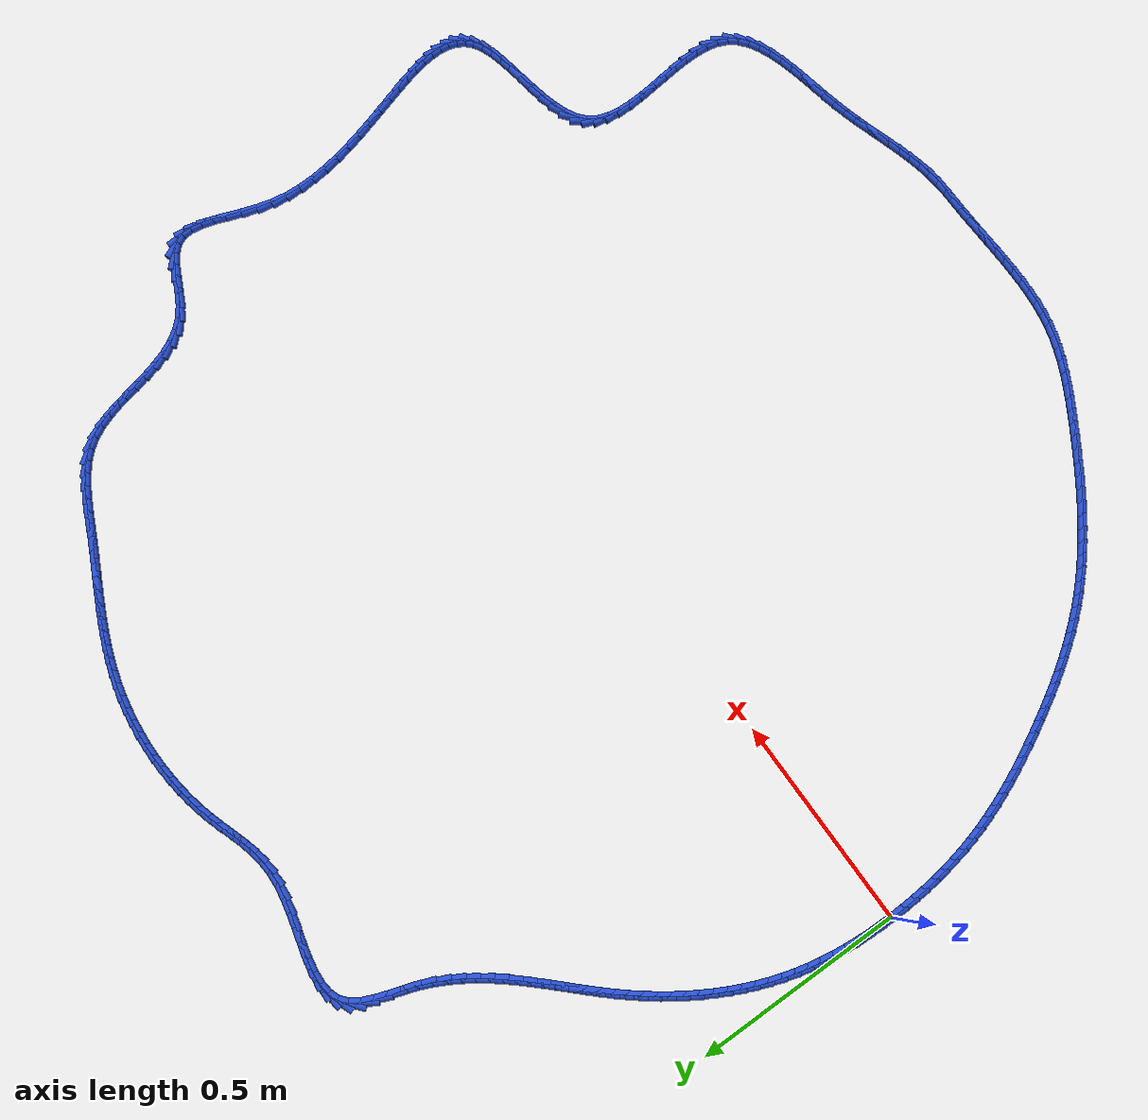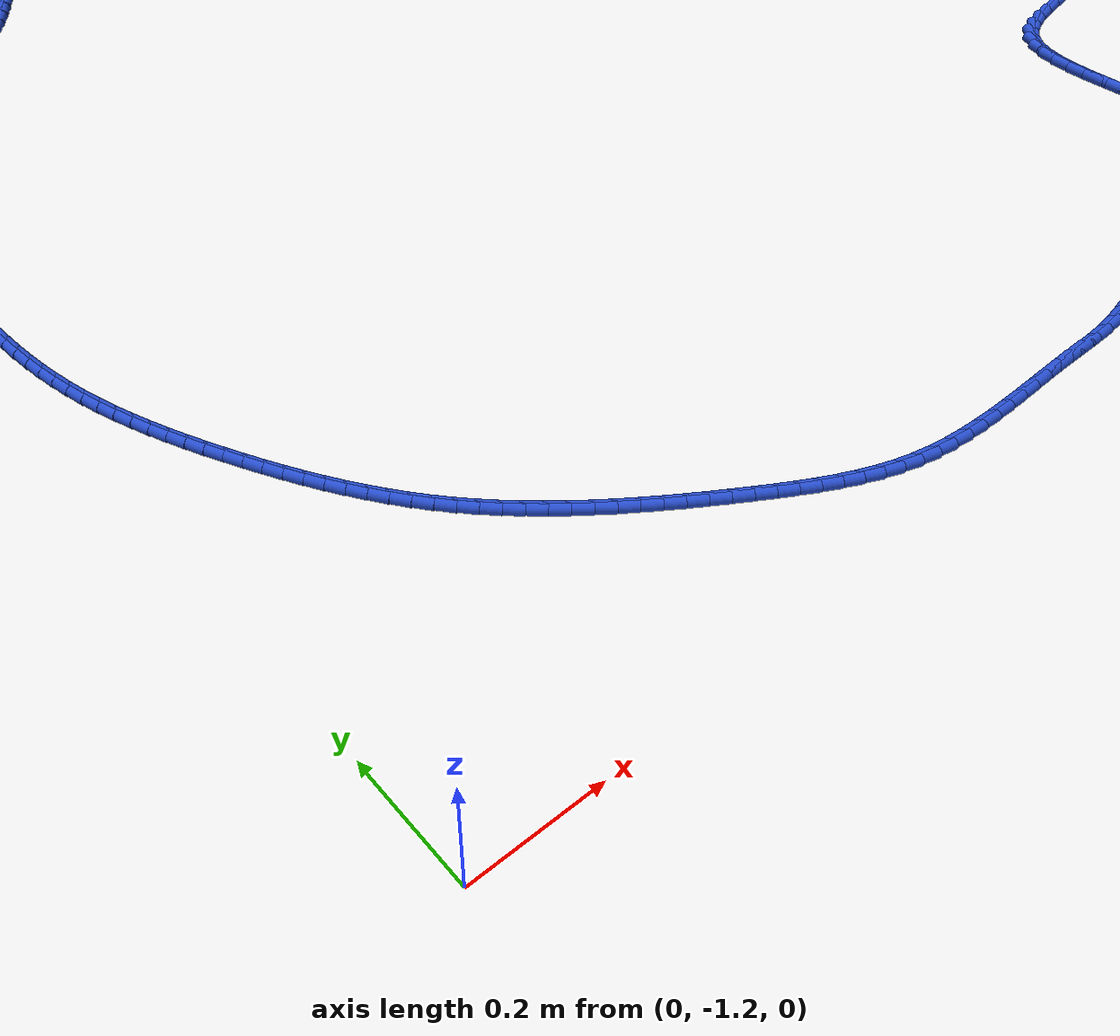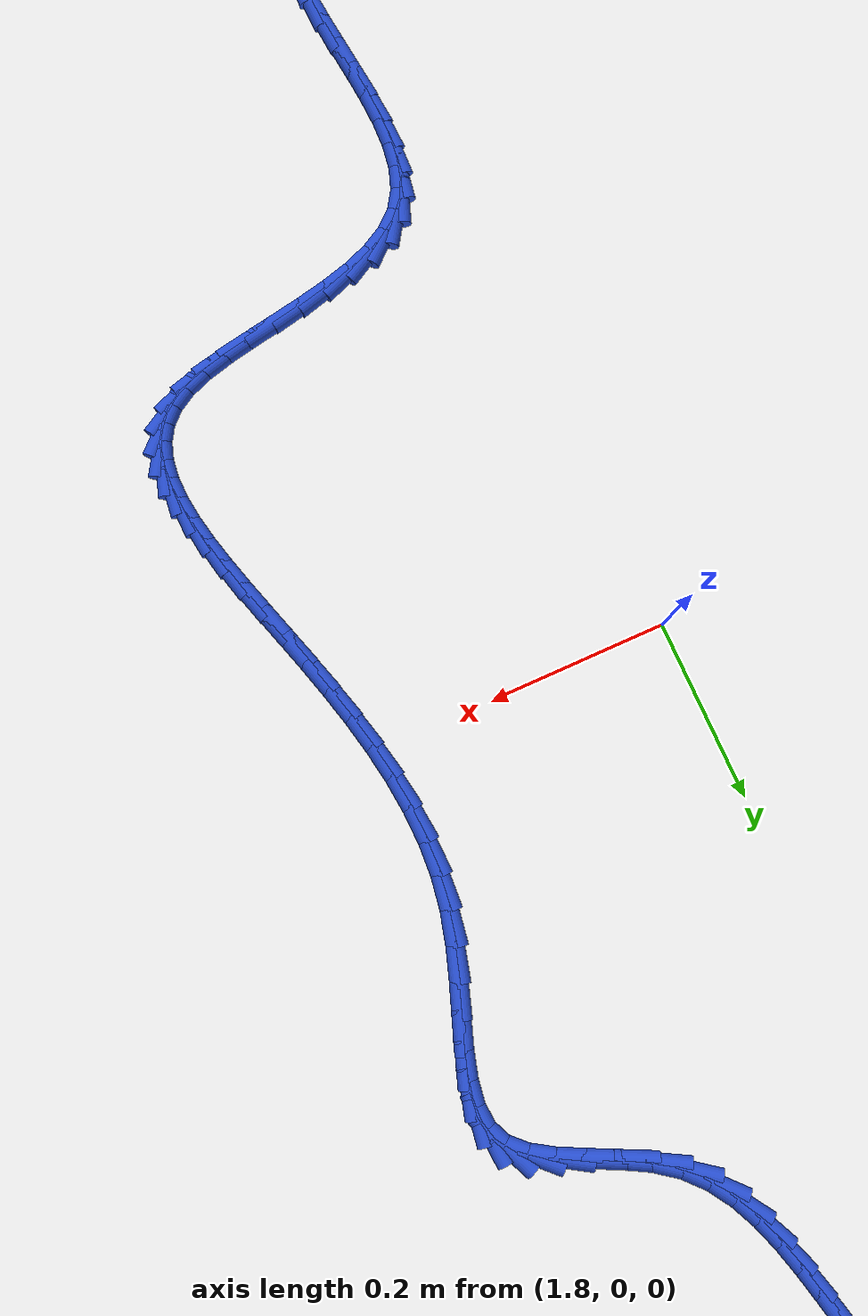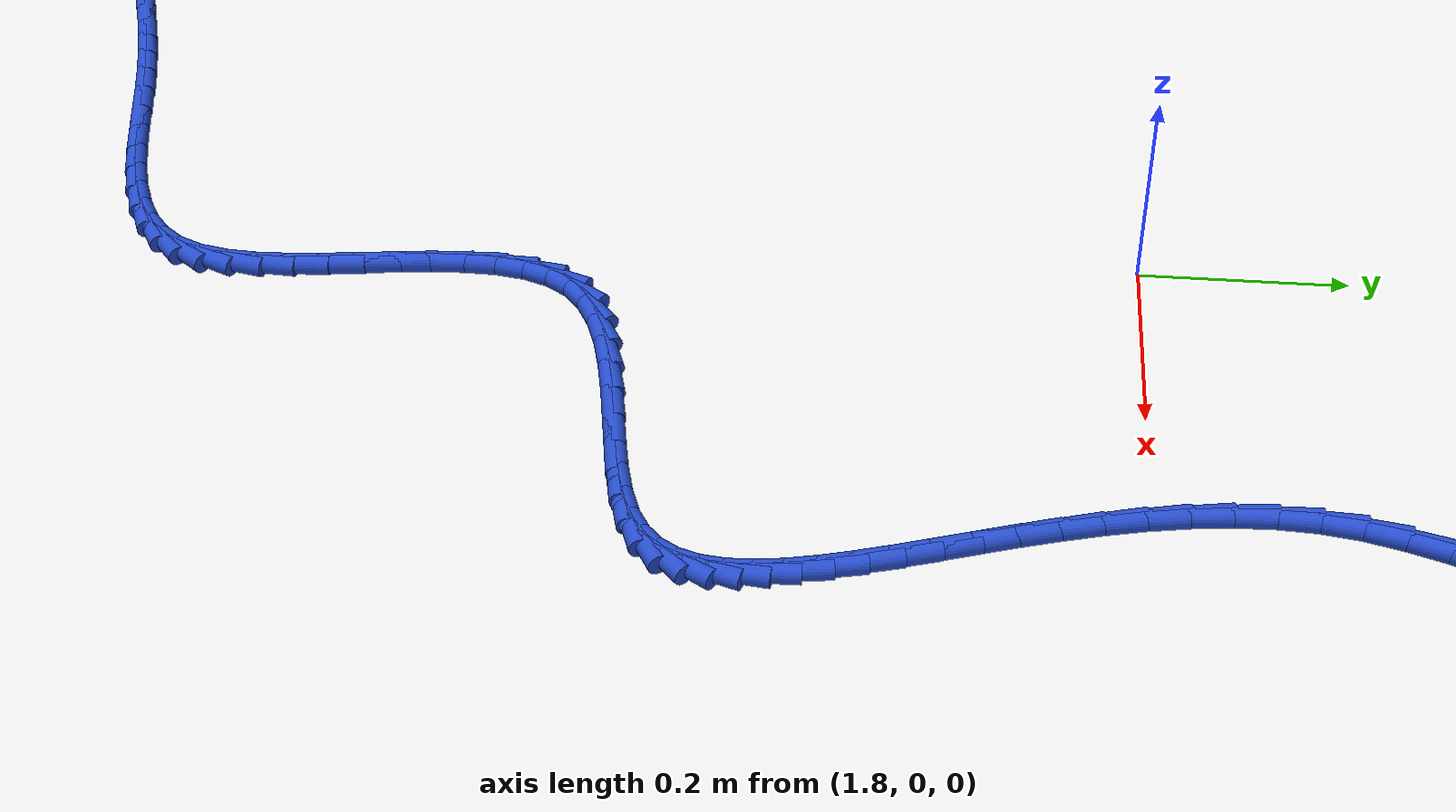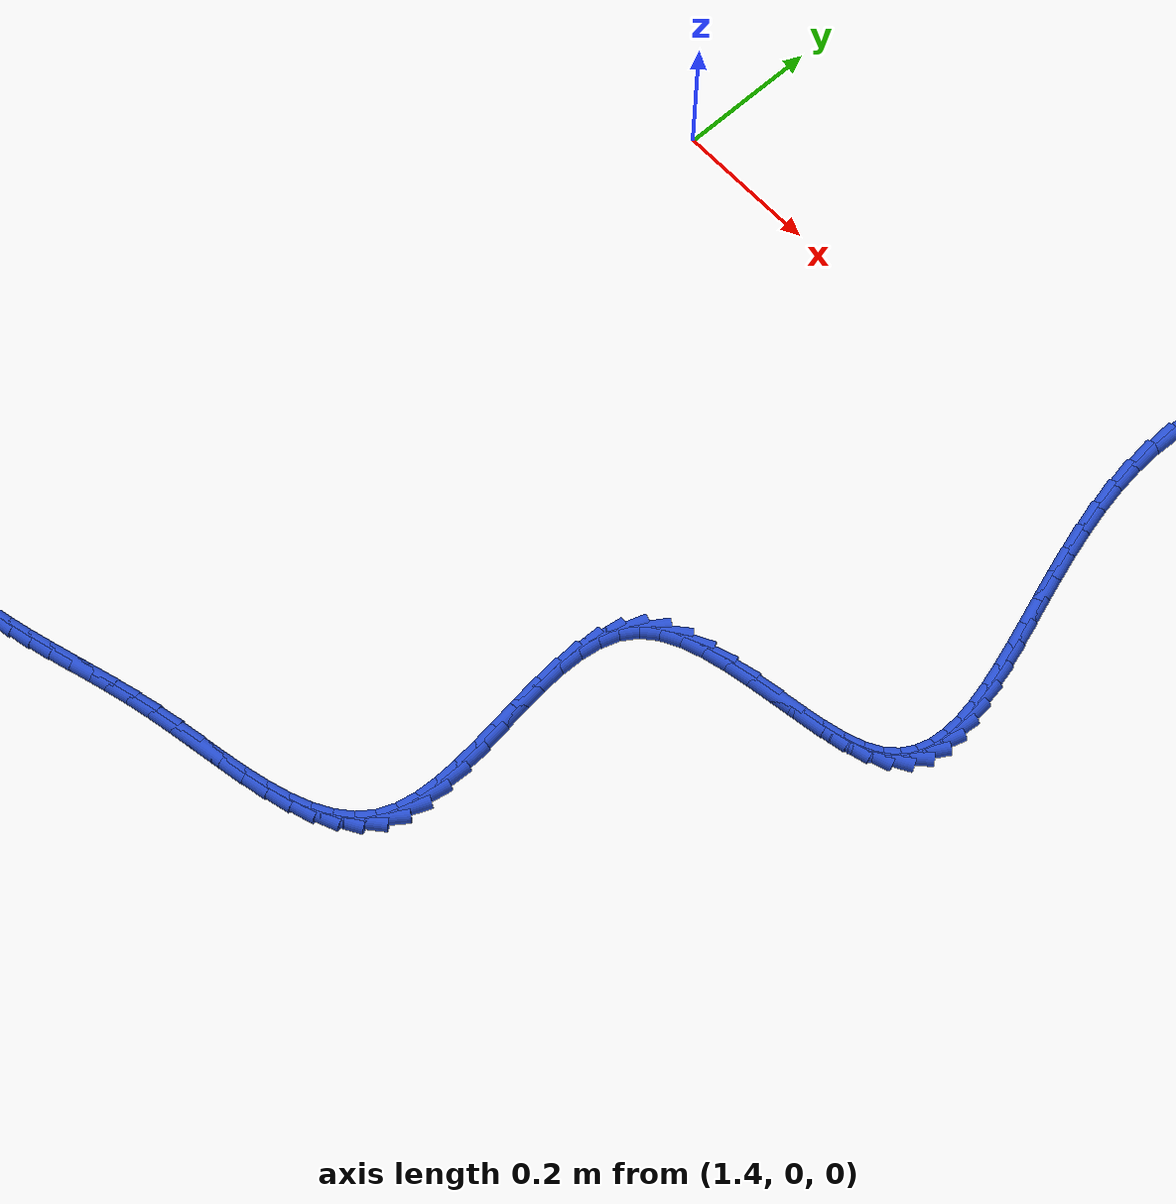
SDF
<sdf version="1.6">
 <world name="default">
  <light name="sun" type="directional">
   <pose>0 0 10 0 -0 0</pose>
   <diffuse>0.8 0.8 0.8 1</diffuse>
   <specular>0.2 0.2 0.2 1</specular>
   <attenuation>
    <range>1000</range>
    <constant>0.9</constant>
    <linear>0.01</linear>
    <quadratic>0.001</quadratic>
   </attenuation>
   <direction>-0.5 0.1 -0.9</direction>
  </light>
  <model name="ground_plane">
   <static>1</static>
   <link name="link">
    <collision name="collision">
     <geometry><plane><normal>0 0 1</normal><size>100 100</size></plane></geometry>
     <surface><friction><ode><mu>100</mu><mu2>50</mu2></ode></friction></surface>
    </collision>
    <visual name="visual">
     <cast_shadows>0</cast_shadows>
     <geometry><plane><normal>0 0 1</normal><size>100 100</size></plane></geometry>
     <material>
      <script><uri>file://media/materials/scripts/gazebo.material</uri><name>Gazebo/WhiteGlow</name></script>
     </material>
    </visual>
   </link>
  </model>
  <gravity>0 0 -9.8</gravity>
  <magnetic_field>6e-06 2.3e-05 -4.2e-05</magnetic_field>
  <atmosphere type="adiabatic"/>
  <physics name="default_physics" default="0" type="ode">
   <max_step_size>0.001</max_step_size>
   <real_time_factor>1</real_time_factor>
   <real_time_update_rate>1000</real_time_update_rate>
  </physics>
  <scene><ambient>0.4 0.4 0.4 1</ambient><background>0.7 0.7 0.7 1</background><shadows>1</shadows></scene>
  <spherical_coordinates>
   <surface_model>EARTH_WGS84</surface_model>
   <latitude_deg>0</latitude_deg>
   <longitude_deg>0</longitude_deg>
   <elevation>0</elevation>
   <heading_deg>0</heading_deg>
  </spherical_coordinates>
  <model name="line">
   <link name="link_0">
    <pose>1.1709383462843448e-17 4.163336342344337e-17 0.01 0 1.57 1.5636640697530726</pose>
    <collision name="collision">
     <geometry><cylinder><radius>0.01</radius><length>0.08</length></cylinder></geometry>
    </collision>
    <visual name="visual">
     <material>
      <script><name>Gazebo/Blue</name><uri>file://media/materials/scripts/gazebo.material</uri></script>
     </material>
     <geometry><cylinder><radius>0.01</radius><length>0.08</length></cylinder></geometry>
    </visual>
   </link>
   <link name="link_1">
    <pose>0.00021605386986257264 0.030291982621384793 0.01 0 1.57 1.5359491459673433</pose>
    <collision name="collision">
     <geometry><cylinder><radius>0.01</radius><length>0.08</length></cylinder></geometry>
    </collision>
    <visual name="visual">
     <material>
      <script><name>Gazebo/Blue</name><uri>file://media/materials/scripts/gazebo.material</uri></script>
     </material>
     <geometry><cylinder><radius>0.01</radius><length>0.08</length></cylinder></geometry>
    </visual>
   </link>
   <link name="link_2">
    <pose>0.0012710043663280038 0.06055335295052828 0.01 0 1.57 1.506263772295638</pose>
    <collision name="collision">
     <geometry><cylinder><radius>0.01</radius><length>0.08</length></cylinder></geometry>
    </collision>
    <visual name="visual">
     <material>
      <script><name>Gazebo/Blue</name><uri>file://media/materials/scripts/gazebo.material</uri></script>
     </material>
     <geometry><cylinder><radius>0.01</radius><length>0.08</length></cylinder></geometry>
    </visual>
   </link>
   <link name="link_3">
    <pose>0.0032218751019634393 0.09074217620428113 0.01 0 1.57 1.474540158930334</pose>
    <collision name="collision">
     <geometry><cylinder><radius>0.01</radius><length>0.08</length></cylinder></geometry>
    </collision>
    <visual name="visual">
     <material>
      <script><name>Gazebo/Blue</name><uri>file://media/materials/scripts/gazebo.material</uri></script>
     </material>
     <geometry><cylinder><radius>0.01</radius><length>0.08</length></cylinder></geometry>
    </visual>
   </link>
   <link name="link_4">
    <pose>0.006125689689336 0.12081651759949373 0.01 0 1.57 1.4407176925384437</pose>
    <collision name="collision">
     <geometry><cylinder><radius>0.01</radius><length>0.08</length></cylinder></geometry>
    </collision>
    <visual name="visual">
     <material>
      <script><name>Gazebo/Blue</name><uri>file://media/materials/scripts/gazebo.material</uri></script>
     </material>
     <geometry><cylinder><radius>0.01</radius><length>0.08</length></cylinder></geometry>
    </visual>
   </link>
   <link name="link_5">
    <pose>0.010039471741012811 0.1507344423530167 0.01 0 1.57 1.4047471201541903</pose>
    <collision name="collision">
     <geometry><cylinder><radius>0.01</radius><length>0.08</length></cylinder></geometry>
    </collision>
    <visual name="visual">
     <material>
      <script><name>Gazebo/Blue</name><uri>file://media/materials/scripts/gazebo.material</uri></script>
     </material>
     <geometry><cylinder><radius>0.01</radius><length>0.08</length></cylinder></geometry>
    </visual>
   </link>
   <link name="link_6">
    <pose>0.015020244869561012 0.18045401568170052 0.01 0 1.57 1.366595375959885</pose>
    <collision name="collision">
     <geometry><cylinder><radius>0.01</radius><length>0.08</length></cylinder></geometry>
    </collision>
    <visual name="visual">
     <material>
      <script><name>Gazebo/Blue</name><uri>file://media/materials/scripts/gazebo.material</uri></script>
     </material>
     <geometry><cylinder><radius>0.01</radius><length>0.08</length></cylinder></geometry>
    </visual>
   </link>
   <link name="link_7">
    <pose>0.021125032687547708 0.2099333028023957 0.01 0 1.57 1.326250966430491</pose>
    <collision name="collision">
     <geometry><cylinder><radius>0.01</radius><length>0.08</length></cylinder></geometry>
    </collision>
    <visual name="visual">
     <material>
      <script><name>Gazebo/Blue</name><uri>file://media/materials/scripts/gazebo.material</uri></script>
     </material>
     <geometry><cylinder><radius>0.01</radius><length>0.08</length></cylinder></geometry>
    </visual>
   </link>
   <link name="link_8">
    <pose>0.028410858807540046 0.23913036893195272 0.01 0 1.57 1.2837508417973633</pose>
    <collision name="collision">
     <geometry><cylinder><radius>0.01</radius><length>0.08</length></cylinder></geometry>
    </collision>
    <visual name="visual">
     <material>
      <script><name>Gazebo/Blue</name><uri>file://media/materials/scripts/gazebo.material</uri></script>
     </material>
     <geometry><cylinder><radius>0.01</radius><length>0.08</length></cylinder></geometry>
    </visual>
   </link>
   <link name="link_9">
    <pose>0.03693411065836092 0.26800336926790747 0.01 0 1.57 1.2405349048784968</pose>
    <collision name="collision">
     <geometry><cylinder><radius>0.01</radius><length>0.08</length></cylinder></geometry>
    </collision>
    <visual name="visual">
     <material>
      <script><name>Gazebo/Blue</name><uri>file://media/materials/scripts/gazebo.material</uri></script>
     </material>
     <geometry><cylinder><radius>0.01</radius><length>0.08</length></cylinder></geometry>
    </visual>
   </link>
   <link name="link_10">
    <pose>0.04670887624633902 0.29651644176208003 0.01 0 1.57 1.1988532899110953</pose>
    <collision name="collision">
     <geometry><cylinder><radius>0.01</radius><length>0.08</length></cylinder></geometry>
    </collision>
    <visual name="visual">
     <material>
      <script><name>Gazebo/Blue</name><uri>file://media/materials/scripts/gazebo.material</uri></script>
     </material>
     <geometry><cylinder><radius>0.01</radius><length>0.08</length></cylinder></geometry>
    </visual>
   </link>
   <link name="link_11">
    <pose>0.057681188571026186 0.3246433499441205 0.01 0 1.57 1.1588626958872574</pose>
    <collision name="collision">
     <geometry><cylinder><radius>0.01</radius><length>0.08</length></cylinder></geometry>
    </collision>
    <visual name="visual">
     <material>
      <script><name>Gazebo/Blue</name><uri>file://media/materials/scripts/gazebo.material</uri></script>
     </material>
     <geometry><cylinder><radius>0.01</radius><length>0.08</length></cylinder></geometry>
    </visual>
   </link>
   <link name="link_12">
    <pose>0.069790925307557 0.3523587279416999 0.01 0 1.57 1.120498247382104</pose>
    <collision name="collision">
     <geometry><cylinder><radius>0.01</radius><length>0.08</length></cylinder></geometry>
    </collision>
    <visual name="visual">
     <material>
      <script><name>Gazebo/Blue</name><uri>file://media/materials/scripts/gazebo.material</uri></script>
     </material>
     <geometry><cylinder><radius>0.01</radius><length>0.08</length></cylinder></geometry>
    </visual>
   </link>
   <link name="link_13">
    <pose>0.08297796413106598 0.37963720988248995 0.01 0 1.57 1.0836816882748765</pose>
    <collision name="collision">
     <geometry><cylinder><radius>0.01</radius><length>0.08</length></cylinder></geometry>
    </collision>
    <visual name="visual">
     <material>
      <script><name>Gazebo/Blue</name><uri>file://media/materials/scripts/gazebo.material</uri></script>
     </material>
     <geometry><cylinder><radius>0.01</radius><length>0.08</length></cylinder></geometry>
    </visual>
   </link>
   <link name="link_14">
    <pose>0.09718218271668772 0.4064534298941617 0.01 0 1.57 1.048324733414023</pose>
    <collision name="collision">
     <geometry><cylinder><radius>0.01</radius><length>0.08</length></cylinder></geometry>
    </collision>
    <visual name="visual">
     <material>
      <script><name>Gazebo/Blue</name><uri>file://media/materials/scripts/gazebo.material</uri></script>
     </material>
     <geometry><cylinder><radius>0.01</radius><length>0.08</length></cylinder></geometry>
    </visual>
   </link>
   <link name="link_15">
    <pose>0.11234345873955673 0.4327820221043867 0.01 0 1.57 1.0143318400632366</pose>
    <collision name="collision">
     <geometry><cylinder><radius>0.01</radius><length>0.08</length></cylinder></geometry>
    </collision>
    <visual name="visual">
     <material>
      <script><name>Gazebo/Blue</name><uri>file://media/materials/scripts/gazebo.material</uri></script>
     </material>
     <geometry><cylinder><radius>0.01</radius><length>0.08</length></cylinder></geometry>
    </visual>
   </link>
   <link name="link_16">
    <pose>0.12840166987480764 0.4585976206408361 0.01 0 1.57 0.981602411229596</pose>
    <collision name="collision">
     <geometry><cylinder><radius>0.01</radius><length>0.08</length></cylinder></geometry>
    </collision>
    <visual name="visual">
     <material>
      <script><name>Gazebo/Blue</name><uri>file://media/materials/scripts/gazebo.material</uri></script>
     </material>
     <geometry><cylinder><radius>0.01</radius><length>0.08</length></cylinder></geometry>
    </visual>
   </link>
   <link name="link_17">
    <pose>0.14529669379757496 0.4838748596311812 0.01 0 1.57 0.9500324685238439</pose>
    <collision name="collision">
     <geometry><cylinder><radius>0.01</radius><length>0.08</length></cylinder></geometry>
    </collision>
    <visual name="visual">
     <material>
      <script><name>Gazebo/Blue</name><uri>file://media/materials/scripts/gazebo.material</uri></script>
     </material>
     <geometry><cylinder><radius>0.01</radius><length>0.08</length></cylinder></geometry>
    </visual>
   </link>
   <link name="link_18">
    <pose>0.1629684081829933 0.5085883732030936 0.01 0 1.57 0.9195158449689439</pose>
    <collision name="collision">
     <geometry><cylinder><radius>0.01</radius><length>0.08</length></cylinder></geometry>
    </collision>
    <visual name="visual">
     <material>
      <script><name>Gazebo/Blue</name><uri>file://media/materials/scripts/gazebo.material</uri></script>
     </material>
     <geometry><cylinder><radius>0.01</radius><length>0.08</length></cylinder></geometry>
    </visual>
   </link>
   <link name="link_19">
    <pose>0.18135669070619712 0.5327127954842444 0.01 0 1.57 0.8899449515929984</pose>
    <collision name="collision">
     <geometry><cylinder><radius>0.01</radius><length>0.08</length></cylinder></geometry>
    </collision>
    <visual name="visual">
     <material>
      <script><name>Gazebo/Blue</name><uri>file://media/materials/scripts/gazebo.material</uri></script>
     </material>
     <geometry><cylinder><radius>0.01</radius><length>0.08</length></cylinder></geometry>
    </visual>
   </link>
   <link name="link_20">
    <pose>0.20040141904232106 0.5562227606023049 0.01 0 1.57 0.8612258308895455</pose>
    <collision name="collision">
     <geometry><cylinder><radius>0.01</radius><length>0.08</length></cylinder></geometry>
    </collision>
    <visual name="visual">
     <material>
      <script><name>Gazebo/Blue</name><uri>file://media/materials/scripts/gazebo.material</uri></script>
     </material>
     <geometry><cylinder><radius>0.01</radius><length>0.08</length></cylinder></geometry>
    </visual>
   </link>
   <link name="link_21">
    <pose>0.2200422611931151 0.5790933369826945 0.01 0 1.57 0.8352723841311117</pose>
    <collision name="collision">
     <geometry><cylinder><radius>0.01</radius><length>0.08</length></cylinder></geometry>
    </collision>
    <visual name="visual">
     <material>
      <script><name>Gazebo/Blue</name><uri>file://media/materials/scripts/gazebo.material</uri></script>
     </material>
     <geometry><cylinder><radius>0.01</radius><length>0.08</length></cylinder></geometry>
    </visual>
   </link>
   <link name="link_22">
    <pose>0.24019040927332286 0.6013585753275388 0.01 0 1.57 0.8161657814089618</pose>
    <collision name="collision">
     <geometry><cylinder><radius>0.01</radius><length>0.08</length></cylinder></geometry>
    </collision>
    <visual name="visual">
     <material>
      <script><name>Gazebo/Blue</name><uri>file://media/materials/scripts/gazebo.material</uri></script>
     </material>
     <geometry><cylinder><radius>0.01</radius><length>0.08</length></cylinder></geometry>
    </visual>
   </link>
   <link name="link_23">
    <pose>0.26069999667171045 0.62317071242263 0.01 0 1.57 0.8044997411409756</pose>
    <collision name="collision">
     <geometry><cylinder><radius>0.01</radius><length>0.08</length></cylinder></geometry>
    </collision>
    <visual name="visual">
     <material>
      <script><name>Gazebo/Blue</name><uri>file://media/materials/scripts/gazebo.material</uri></script>
     </material>
     <geometry><cylinder><radius>0.01</radius><length>0.08</length></cylinder></geometry>
    </visual>
   </link>
   <link name="link_24">
    <pose>0.28141834943339783 0.6446960851457605 0.01 0 1.57 0.8003451342596903</pose>
    <collision name="collision">
     <geometry><cylinder><radius>0.01</radius><length>0.08</length></cylinder></geometry>
    </collision>
    <visual name="visual">
     <material>
      <script><name>Gazebo/Blue</name><uri>file://media/materials/scripts/gazebo.material</uri></script>
     </material>
     <geometry><cylinder><radius>0.01</radius><length>0.08</length></cylinder></geometry>
    </visual>
   </link>
   <link name="link_25">
    <pose>0.3021927936035044 0.6661010303747226 0.01 0 1.57 0.8037444679993899</pose>
    <collision name="collision">
     <geometry><cylinder><radius>0.01</radius><length>0.08</length></cylinder></geometry>
    </collision>
    <visual name="visual">
     <material>
      <script><name>Gazebo/Blue</name><uri>file://media/materials/scripts/gazebo.material</uri></script>
     </material>
     <geometry><cylinder><radius>0.01</radius><length>0.08</length></cylinder></geometry>
    </visual>
   </link>
   <link name="link_26">
    <pose>0.3228706552271501 0.6875518849873091 0.01 0 1.57 0.8147184759105414</pose>
    <collision name="collision">
     <geometry><cylinder><radius>0.01</radius><length>0.08</length></cylinder></geometry>
    </collision>
    <visual name="visual">
     <material>
      <script><name>Gazebo/Blue</name><uri>file://media/materials/scripts/gazebo.material</uri></script>
     </material>
     <geometry><cylinder><radius>0.01</radius><length>0.08</length></cylinder></geometry>
    </visual>
   </link>
   <link name="link_27">
    <pose>0.3432992603494545 0.709214985861312 0.01 0 1.57 0.8332600373029755</pose>
    <collision name="collision">
     <geometry><cylinder><radius>0.01</radius><length>0.08</length></cylinder></geometry>
    </collision>
    <visual name="visual">
     <material>
      <script><name>Gazebo/Blue</name><uri>file://media/materials/scripts/gazebo.material</uri></script>
     </material>
     <geometry><cylinder><radius>0.01</radius><length>0.08</length></cylinder></geometry>
    </visual>
   </link>
   <link name="link_28">
    <pose>0.3633259350155376 0.7312566698745246 0.01 0 1.57 0.8593153615482799</pose>
    <collision name="collision">
     <geometry><cylinder><radius>0.01</radius><length>0.08</length></cylinder></geometry>
    </collision>
    <visual name="visual">
     <material>
      <script><name>Gazebo/Blue</name><uri>file://media/materials/scripts/gazebo.material</uri></script>
     </material>
     <geometry><cylinder><radius>0.01</radius><length>0.08</length></cylinder></geometry>
    </visual>
   </link>
   <link name="link_29">
    <pose>0.38279800527051877 0.7538432739047387 0.01 0 1.57 0.8927532781186259</pose>
    <collision name="collision">
     <geometry><cylinder><radius>0.01</radius><length>0.08</length></cylinder></geometry>
    </collision>
    <visual name="visual">
     <material>
      <script><name>Gazebo/Blue</name><uri>file://media/materials/scripts/gazebo.material</uri></script>
     </material>
     <geometry><cylinder><radius>0.01</radius><length>0.08</length></cylinder></geometry>
    </visual>
   </link>
   <link name="link_30">
    <pose>0.40156279715951815 0.7771411348297471 0.01 0 1.57 0.9333251137065224</pose>
    <collision name="collision">
     <geometry><cylinder><radius>0.01</radius><length>0.08</length></cylinder></geometry>
    </collision>
    <visual name="visual">
     <material>
      <script><name>Gazebo/Blue</name><uri>file://media/materials/scripts/gazebo.material</uri></script>
     </material>
     <geometry><cylinder><radius>0.01</radius><length>0.08</length></cylinder></geometry>
    </visual>
   </link>
   <link name="link_31">
    <pose>0.4194676367276551 0.8013165895273421 0.01 0 1.57 0.9806202657049099</pose>
    <collision name="collision">
     <geometry><cylinder><radius>0.01</radius><length>0.08</length></cylinder></geometry>
    </collision>
    <visual name="visual">
     <material>
      <script><name>Gazebo/Blue</name><uri>file://media/materials/scripts/gazebo.material</uri></script>
     </material>
     <geometry><cylinder><radius>0.01</radius><length>0.08</length></cylinder></geometry>
    </visual>
   </link>
   <link name="link_32">
    <pose>0.43635985002004973 0.8265359748753168 0.01 0 1.57 1.0340259318108969</pose>
    <collision name="collision">
     <geometry><cylinder><radius>0.01</radius><length>0.08</length></cylinder></geometry>
    </collision>
    <visual name="visual">
     <material>
      <script><name>Gazebo/Blue</name><uri>file://media/materials/scripts/gazebo.material</uri></script>
     </material>
     <geometry><cylinder><radius>0.01</radius><length>0.08</length></cylinder></geometry>
    </visual>
   </link>
   <link name="link_33">
    <pose>0.4520867630818216 0.8529656277514635 0.01 0 1.57 1.092702429602605</pose>
    <collision name="collision">
     <geometry><cylinder><radius>0.01</radius><length>0.08</length></cylinder></geometry>
    </collision>
    <visual name="visual">
     <material>
      <script><name>Gazebo/Blue</name><uri>file://media/materials/scripts/gazebo.material</uri></script>
     </material>
     <geometry><cylinder><radius>0.01</radius><length>0.08</length></cylinder></geometry>
    </visual>
   </link>
   <link name="link_34">
    <pose>0.4664957019580902 0.8807718850335737 0.01 0 1.57 1.1555862009645406</pose>
    <collision name="collision">
     <geometry><cylinder><radius>0.01</radius><length>0.08</length></cylinder></geometry>
    </collision>
    <visual name="visual">
     <material>
      <script><name>Gazebo/Blue</name><uri>file://media/materials/scripts/gazebo.material</uri></script>
     </material>
     <geometry><cylinder><radius>0.01</radius><length>0.08</length></cylinder></geometry>
    </visual>
   </link>
   <link name="link_35">
    <pose>0.4794339926939757 0.9101210835994413 0.01 0 1.57 1.2190289553433187</pose>
    <collision name="collision">
     <geometry><cylinder><radius>0.01</radius><length>0.08</length></cylinder></geometry>
    </collision>
    <visual name="visual">
     <material>
      <script><name>Gazebo/Blue</name><uri>file://media/materials/scripts/gazebo.material</uri></script>
     </material>
     <geometry><cylinder><radius>0.01</radius><length>0.08</length></cylinder></geometry>
    </visual>
   </link>
   <link name="link_36">
    <pose>0.4908032090118609 0.9410971183664197 0.01 0 1.57 1.2514235744648878</pose>
    <collision name="collision">
     <geometry><cylinder><radius>0.01</radius><length>0.08</length></cylinder></geometry>
    </collision>
    <visual name="visual">
     <material>
      <script><name>Gazebo/Blue</name><uri>file://media/materials/scripts/gazebo.material</uri></script>
     </material>
     <geometry><cylinder><radius>0.01</radius><length>0.08</length></cylinder></geometry>
    </visual>
   </link>
   <link name="link_37">
    <pose>0.5012420523603142 0.9726636472591392 0.01 0 1.57 1.2320879929810282</pose>
    <collision name="collision">
     <geometry><cylinder><radius>0.01</radius><length>0.08</length></cylinder></geometry>
    </collision>
    <visual name="visual">
     <material>
      <script><name>Gazebo/Blue</name><uri>file://media/materials/scripts/gazebo.material</uri></script>
     </material>
     <geometry><cylinder><radius>0.01</radius><length>0.08</length></cylinder></geometry>
    </visual>
   </link>
   <link name="link_38">
    <pose>0.5119207896846295 1.0029764908189152 0.01 0 1.57 1.152171597398014</pose>
    <collision name="collision">
     <geometry><cylinder><radius>0.01</radius><length>0.08</length></cylinder></geometry>
    </collision>
    <visual name="visual">
     <material>
      <script><name>Gazebo/Blue</name><uri>file://media/materials/scripts/gazebo.material</uri></script>
     </material>
     <geometry><cylinder><radius>0.01</radius><length>0.08</length></cylinder></geometry>
    </visual>
   </link>
   <link name="link_39">
    <pose>0.5240214406705371 1.0301736085649718 0.01 0 1.57 0.9861762365949805</pose>
    <collision name="collision">
     <geometry><cylinder><radius>0.01</radius><length>0.08</length></cylinder></geometry>
    </collision>
    <visual name="visual">
     <material>
      <script><name>Gazebo/Blue</name><uri>file://media/materials/scripts/gazebo.material</uri></script>
     </material>
     <geometry><cylinder><radius>0.01</radius><length>0.08</length></cylinder></geometry>
    </visual>
   </link>
   <link name="link_40">
    <pose>0.5387260250037664 1.0523929600165334 0.01 0 1.57 0.6990106509107171</pose>
    <collision name="collision">
     <geometry><cylinder><radius>0.01</radius><length>0.08</length></cylinder></geometry>
    </collision>
    <visual name="visual">
     <material>
      <script><name>Gazebo/Blue</name><uri>file://media/materials/scripts/gazebo.material</uri></script>
     </material>
     <geometry><cylinder><radius>0.01</radius><length>0.08</length></cylinder></geometry>
    </visual>
   </link>
   <link name="link_41">
    <pose>0.5571528322739582 1.0678825074071845 0.01 0 1.57 0.3690520572561279</pose>
    <collision name="collision">
     <geometry><cylinder><radius>0.01</radius><length>0.08</length></cylinder></geometry>
    </collision>
    <visual name="visual">
     <material>
      <script><name>Gazebo/Blue</name><uri>file://media/materials/scripts/gazebo.material</uri></script>
     </material>
     <geometry><cylinder><radius>0.01</radius><length>0.08</length></cylinder></geometry>
    </visual>
   </link>
   <link name="link_42">
    <pose>0.5794776001551023 1.0765171251440122 0.01 0 1.57 0.11235421229624952</pose>
    <collision name="collision">
     <geometry><cylinder><radius>0.01</radius><length>0.08</length></cylinder></geometry>
    </collision>
    <visual name="visual">
     <material>
      <script><name>Gazebo/Blue</name><uri>file://media/materials/scripts/gazebo.material</uri></script>
     </material>
     <geometry><cylinder><radius>0.01</radius><length>0.08</length></cylinder></geometry>
    </visual>
   </link>
   <link name="link_43">
    <pose>0.6051560928197762 1.0794144135090438 0.01 0 1.57 -0.05932756533106323</pose>
    <collision name="collision">
     <geometry><cylinder><radius>0.01</radius><length>0.08</length></cylinder></geometry>
    </collision>
    <visual name="visual">
     <material>
      <script><name>Gazebo/Blue</name><uri>file://media/materials/scripts/gazebo.material</uri></script>
     </material>
     <geometry><cylinder><radius>0.01</radius><length>0.08</length></cylinder></geometry>
    </visual>
   </link>
   <link name="link_44">
    <pose>0.6336258750874274 1.0777233861724307 0.01 0 1.57 -0.16558887690210264</pose>
    <collision name="collision">
     <geometry><cylinder><radius>0.01</radius><length>0.08</length></cylinder></geometry>
    </collision>
    <visual name="visual">
     <material>
      <script><name>Gazebo/Blue</name><uri>file://media/materials/scripts/gazebo.material</uri></script>
     </material>
     <geometry><cylinder><radius>0.01</radius><length>0.08</length></cylinder></geometry>
    </visual>
   </link>
   <link name="link_45">
    <pose>0.6643245117775041 1.0725930568043238 0.01 0 1.57 -0.22538321337407694</pose>
    <collision name="collision">
     <geometry><cylinder><radius>0.01</radius><length>0.08</length></cylinder></geometry>
    </collision>
    <visual name="visual">
     <material>
      <script><name>Gazebo/Blue</name><uri>file://media/materials/scripts/gazebo.material</uri></script>
     </material>
     <geometry><cylinder><radius>0.01</radius><length>0.08</length></cylinder></geometry>
    </visual>
   </link>
   <link name="link_46">
    <pose>0.696689567709454 1.065172439074876 0.01 0 1.57 -0.25044435100764334</pose>
    <collision name="collision">
     <geometry><cylinder><radius>0.01</radius><length>0.08</length></cylinder></geometry>
    </collision>
    <visual name="visual">
     <material>
      <script><name>Gazebo/Blue</name><uri>file://media/materials/scripts/gazebo.material</uri></script>
     </material>
     <geometry><cylinder><radius>0.01</radius><length>0.08</length></cylinder></geometry>
    </visual>
   </link>
   <link name="link_47">
    <pose>0.7301586077027259 1.0566105466542386 0.01 0 1.57 -0.24640348835087936</pose>
    <collision name="collision">
     <geometry><cylinder><radius>0.01</radius><length>0.08</length></cylinder></geometry>
    </collision>
    <visual name="visual">
     <material>
      <script><name>Gazebo/Blue</name><uri>file://media/materials/scripts/gazebo.material</uri></script>
     </material>
     <geometry><cylinder><radius>0.01</radius><length>0.08</length></cylinder></geometry>
    </visual>
   </link>
   <link name="link_48">
    <pose>0.7641691965767673 1.0480563932125637 0.01 0 1.57 -0.214294827461099</pose>
    <collision name="collision">
     <geometry><cylinder><radius>0.01</radius><length>0.08</length></cylinder></geometry>
    </collision>
    <visual name="visual">
     <material>
      <script><name>Gazebo/Blue</name><uri>file://media/materials/scripts/gazebo.material</uri></script>
     </material>
     <geometry><cylinder><radius>0.01</radius><length>0.08</length></cylinder></geometry>
    </visual>
   </link>
   <link name="link_49">
    <pose>0.798158899151026 1.040658992420003 0.01 0 1.57 -0.15125099124943975</pose>
    <collision name="collision">
     <geometry><cylinder><radius>0.01</radius><length>0.08</length></cylinder></geometry>
    </collision>
    <visual name="visual">
     <material>
      <script><name>Gazebo/Blue</name><uri>file://media/materials/scripts/gazebo.material</uri></script>
     </material>
     <geometry><cylinder><radius>0.01</radius><length>0.08</length></cylinder></geometry>
    </visual>
   </link>
   <link name="link_50">
    <pose>0.8315652802449507 1.0355673579467077 0.01 0 1.57 -0.05091314864187035</pose>
    <collision name="collision">
     <geometry><cylinder><radius>0.01</radius><length>0.08</length></cylinder></geometry>
    </collision>
    <visual name="visual">
     <material>
      <script><name>Gazebo/Blue</name><uri>file://media/materials/scripts/gazebo.material</uri></script>
     </material>
     <geometry><cylinder><radius>0.01</radius><length>0.08</length></cylinder></geometry>
    </visual>
   </link>
   <link name="link_51">
    <pose>0.8638290824509341 1.0339232853835068 0.01 0 1.57 0.07329513712206373</pose>
    <collision name="collision">
     <geometry><cylinder><radius>0.01</radius><length>0.08</length></cylinder></geometry>
    </collision>
    <visual name="visual">
     <material>
      <script><name>Gazebo/Blue</name><uri>file://media/materials/scripts/gazebo.material</uri></script>
     </material>
     <geometry><cylinder><radius>0.01</radius><length>0.08</length></cylinder></geometry>
    </visual>
   </link>
   <link name="link_52">
    <pose>0.8946900953837537 1.0361893068350465 0.01 0 1.57 0.18004484692380715</pose>
    <collision name="collision">
     <geometry><cylinder><radius>0.01</radius><length>0.08</length></cylinder></geometry>
    </collision>
    <visual name="visual">
     <material>
      <script><name>Gazebo/Blue</name><uri>file://media/materials/scripts/gazebo.material</uri></script>
     </material>
     <geometry><cylinder><radius>0.01</radius><length>0.08</length></cylinder></geometry>
    </visual>
   </link>
   <link name="link_53">
    <pose>0.924427817997376 1.0416020440312794 0.01 0 1.57 0.2589014758136229</pose>
    <collision name="collision">
     <geometry><cylinder><radius>0.01</radius><length>0.08</length></cylinder></geometry>
    </collision>
    <visual name="visual">
     <material>
      <script><name>Gazebo/Blue</name><uri>file://media/materials/scripts/gazebo.material</uri></script>
     </material>
     <geometry><cylinder><radius>0.01</radius><length>0.08</length></cylinder></geometry>
    </visual>
   </link>
   <link name="link_54">
    <pose>0.9533783849188437 1.0492694749041707 0.01 0 1.57 0.3068436168448405</pose>
    <collision name="collision">
     <geometry><cylinder><radius>0.01</radius><length>0.08</length></cylinder></geometry>
    </collision>
    <visual name="visual">
     <material>
      <script><name>Gazebo/Blue</name><uri>file://media/materials/scripts/gazebo.material</uri></script>
     </material>
     <geometry><cylinder><radius>0.01</radius><length>0.08</length></cylinder></geometry>
    </visual>
   </link>
   <link name="link_55">
    <pose>0.9818779307751996 1.0582995773856865 0.01 0 1.57 0.32299292851977285</pose>
    <collision name="collision">
     <geometry><cylinder><radius>0.01</radius><length>0.08</length></cylinder></geometry>
    </collision>
    <visual name="visual">
     <material>
      <script><name>Gazebo/Blue</name><uri>file://media/materials/scripts/gazebo.material</uri></script>
     </material>
     <geometry><cylinder><radius>0.01</radius><length>0.08</length></cylinder></geometry>
    </visual>
   </link>
   <link name="link_56">
    <pose>1.0102625901934863 1.0678003294077925 0.01 0 1.57 0.3073383712178518</pose>
    <collision name="collision">
     <geometry><cylinder><radius>0.01</radius><length>0.08</length></cylinder></geometry>
    </collision>
    <visual name="visual">
     <material>
      <script><name>Gazebo/Blue</name><uri>file://media/materials/scripts/gazebo.material</uri></script>
     </material>
     <geometry><cylinder><radius>0.01</radius><length>0.08</length></cylinder></geometry>
    </visual>
   </link>
   <link name="link_57">
    <pose>1.0388684978007463 1.0768797089024544 0.01 0 1.57 0.2641203409737604</pose>
    <collision name="collision">
     <geometry><cylinder><radius>0.01</radius><length>0.08</length></cylinder></geometry>
    </collision>
    <visual name="visual">
     <material>
      <script><name>Gazebo/Blue</name><uri>file://media/materials/scripts/gazebo.material</uri></script>
     </material>
     <geometry><cylinder><radius>0.01</radius><length>0.08</length></cylinder></geometry>
    </visual>
   </link>
   <link name="link_58">
    <pose>1.0679804180354708 1.0847526881396043 0.01 0 1.57 0.21522861653261816</pose>
    <collision name="collision">
     <geometry><cylinder><radius>0.01</radius><length>0.08</length></cylinder></geometry>
    </collision>
    <visual name="visual">
     <material>
      <script><name>Gazebo/Blue</name><uri>file://media/materials/scripts/gazebo.material</uri></script>
     </material>
     <geometry><cylinder><radius>0.01</radius><length>0.08</length></cylinder></geometry>
    </visual>
   </link>
   <link name="link_59">
    <pose>1.097598239940221 1.091227580687883 0.01 0 1.57 0.1679145571799948</pose>
    <collision name="collision">
     <geometry><cylinder><radius>0.01</radius><length>0.08</length></cylinder></geometry>
    </collision>
    <visual name="visual">
     <material>
      <script><name>Gazebo/Blue</name><uri>file://media/materials/scripts/gazebo.material</uri></script>
     </material>
     <geometry><cylinder><radius>0.01</radius><length>0.08</length></cylinder></geometry>
    </visual>
   </link>
   <link name="link_60">
    <pose>1.1276236626847076 1.0963172109564971 0.01 0 1.57 0.12193788058899117</pose>
    <collision name="collision">
     <geometry><cylinder><radius>0.01</radius><length>0.08</length></cylinder></geometry>
    </collision>
    <visual name="visual">
     <material>
      <script><name>Gazebo/Blue</name><uri>file://media/materials/scripts/gazebo.material</uri></script>
     </material>
     <geometry><cylinder><radius>0.01</radius><length>0.08</length></cylinder></geometry>
    </visual>
   </link>
   <link name="link_61">
    <pose>1.1579582937760833 1.1000345942703362 0.01 0 1.57 0.07704858479929733</pose>
    <collision name="collision">
     <geometry><cylinder><radius>0.01</radius><length>0.08</length></cylinder></geometry>
    </collision>
    <visual name="visual">
     <material>
      <script><name>Gazebo/Blue</name><uri>file://media/materials/scripts/gazebo.material</uri></script>
     </material>
     <geometry><cylinder><radius>0.01</radius><length>0.08</length></cylinder></geometry>
    </visual>
   </link>
   <link name="link_62">
    <pose>1.1885037407215007 1.1023927459542893 0.01 0 1.57 0.03299538136397213</pose>
    <collision name="collision">
     <geometry><cylinder><radius>0.01</radius><length>0.08</length></cylinder></geometry>
    </collision>
    <visual name="visual">
     <material>
      <script><name>Gazebo/Blue</name><uri>file://media/materials/scripts/gazebo.material</uri></script>
     </material>
     <geometry><cylinder><radius>0.01</radius><length>0.08</length></cylinder></geometry>
    </visual>
   </link>
   <link name="link_63">
    <pose>1.2191616110281127 1.1034046813332463 0.01 0 1.57 -0.01047388133471727</pose>
    <collision name="collision">
     <geometry><cylinder><radius>0.01</radius><length>0.08</length></cylinder></geometry>
    </collision>
    <visual name="visual">
     <material>
      <script><name>Gazebo/Blue</name><uri>file://media/materials/scripts/gazebo.material</uri></script>
     </material>
     <geometry><cylinder><radius>0.01</radius><length>0.08</length></cylinder></geometry>
    </visual>
   </link>
   <link name="link_64">
    <pose>1.249833512203072 1.103083415732097 0.01 0 1.57 -0.0536126245257303</pose>
    <collision name="collision">
     <geometry><cylinder><radius>0.01</radius><length>0.08</length></cylinder></geometry>
    </collision>
    <visual name="visual">
     <material>
      <script><name>Gazebo/Blue</name><uri>file://media/materials/scripts/gazebo.material</uri></script>
     </material>
     <geometry><cylinder><radius>0.01</radius><length>0.08</length></cylinder></geometry>
    </visual>
   </link>
   <link name="link_65">
    <pose>1.2804210517535308 1.1014419644757312 0.01 0 1.57 -0.09667654379611802</pose>
    <collision name="collision">
     <geometry><cylinder><radius>0.01</radius><length>0.08</length></cylinder></geometry>
    </collision>
    <visual name="visual">
     <material>
      <script><name>Gazebo/Blue</name><uri>file://media/materials/scripts/gazebo.material</uri></script>
     </material>
     <geometry><cylinder><radius>0.01</radius><length>0.08</length></cylinder></geometry>
    </visual>
   </link>
   <link name="link_66">
    <pose>1.3108258371866428 1.0984933428890373 0.01 0 1.57 -0.13992501433444052</pose>
    <collision name="collision">
     <geometry><cylinder><radius>0.01</radius><length>0.08</length></cylinder></geometry>
    </collision>
    <visual name="visual">
     <material>
      <script><name>Gazebo/Blue</name><uri>file://media/materials/scripts/gazebo.material</uri></script>
     </material>
     <geometry><cylinder><radius>0.01</radius><length>0.08</length></cylinder></geometry>
    </visual>
   </link>
   <link name="link_67">
    <pose>1.3409494760095602 1.0942505662969064 0.01 0 1.57 -0.18362271742699401</pose>
    <collision name="collision">
     <geometry><cylinder><radius>0.01</radius><length>0.08</length></cylinder></geometry>
    </collision>
    <visual name="visual">
     <material>
      <script><name>Gazebo/Blue</name><uri>file://media/materials/scripts/gazebo.material</uri></script>
     </material>
     <geometry><cylinder><radius>0.01</radius><length>0.08</length></cylinder></geometry>
    </visual>
   </link>
   <link name="link_68">
    <pose>1.3706935757294356 1.0887266500242272 0.01 0 1.57 -0.22804130920534815</pose>
    <collision name="collision">
     <geometry><cylinder><radius>0.01</radius><length>0.08</length></cylinder></geometry>
    </collision>
    <visual name="visual">
     <material>
      <script><name>Gazebo/Blue</name><uri>file://media/materials/scripts/gazebo.material</uri></script>
     </material>
     <geometry><cylinder><radius>0.01</radius><length>0.08</length></cylinder></geometry>
    </visual>
   </link>
   <link name="link_69">
    <pose>1.399959743853422 1.0819346093958897 0.01 0 1.57 -0.27314064011513567</pose>
    <collision name="collision">
     <geometry><cylinder><radius>0.01</radius><length>0.08</length></cylinder></geometry>
    </collision>
    <visual name="visual">
     <material>
      <script><name>Gazebo/Blue</name><uri>file://media/materials/scripts/gazebo.material</uri></script>
     </material>
     <geometry><cylinder><radius>0.01</radius><length>0.08</length></cylinder></geometry>
    </visual>
   </link>
   <link name="link_70">
    <pose>1.4286609782781352 1.0738941799688617 0.01 0 1.57 -0.31568889287929874</pose>
    <collision name="collision">
     <geometry><cylinder><radius>0.01</radius><length>0.08</length></cylinder></geometry>
    </collision>
    <visual name="visual">
     <material>
      <script><name>Gazebo/Blue</name><uri>file://media/materials/scripts/gazebo.material</uri></script>
     </material>
     <geometry><cylinder><radius>0.01</radius><length>0.08</length></cylinder></geometry>
    </visual>
   </link>
   <link name="link_71">
    <pose>1.456827944930706 1.064694520428787 0.01 0 1.57 -0.3533522785203286</pose>
    <collision name="collision">
     <geometry><cylinder><radius>0.01</radius><length>0.08</length></cylinder></geometry>
    </collision>
    <visual name="visual">
     <material>
      <script><name>Gazebo/Blue</name><uri>file://media/materials/scripts/gazebo.material</uri></script>
     </material>
     <geometry><cylinder><radius>0.01</radius><length>0.08</length></cylinder></geometry>
    </visual>
   </link>
   <link name="link_72">
    <pose>1.484560763086737 1.0544657663411499 0.01 0 1.57 -0.38575921719246875</pose>
    <collision name="collision">
     <geometry><cylinder><radius>0.01</radius><length>0.08</length></cylinder></geometry>
    </collision>
    <visual name="visual">
     <material>
      <script><name>Gazebo/Blue</name><uri>file://media/materials/scripts/gazebo.material</uri></script>
     </material>
     <geometry><cylinder><radius>0.01</radius><length>0.08</length></cylinder></geometry>
    </visual>
   </link>
   <link name="link_73">
    <pose>1.5119604510733182 1.0433385837041018 0.01 0 1.57 -0.4126924981171364</pose>
    <collision name="collision">
     <geometry><cylinder><radius>0.01</radius><length>0.08</length></cylinder></geometry>
    </collision>
    <visual name="visual">
     <material>
      <script><name>Gazebo/Blue</name><uri>file://media/materials/scripts/gazebo.material</uri></script>
     </material>
     <geometry><cylinder><radius>0.01</radius><length>0.08</length></cylinder></geometry>
    </visual>
   </link>
   <link name="link_74">
    <pose>1.5391280272175378 1.0314436385157928 0.01 0 1.57 -0.43404288449702344</pose>
    <collision name="collision">
     <geometry><cylinder><radius>0.01</radius><length>0.08</length></cylinder></geometry>
    </collision>
    <visual name="visual">
     <material>
      <script><name>Gazebo/Blue</name><uri>file://media/materials/scripts/gazebo.material</uri></script>
     </material>
     <geometry><cylinder><radius>0.01</radius><length>0.08</length></cylinder></geometry>
    </visual>
   </link>
   <link name="link_75">
    <pose>1.5661645098464838 1.0189115967743727 0.01 0 1.57 -0.4497865280194924</pose>
    <collision name="collision">
     <geometry><cylinder><radius>0.01</radius><length>0.08</length></cylinder></geometry>
    </collision>
    <visual name="visual">
     <material>
      <script><name>Gazebo/Blue</name><uri>file://media/materials/scripts/gazebo.material</uri></script>
     </material>
     <geometry><cylinder><radius>0.01</radius><length>0.08</length></cylinder></geometry>
    </visual>
   </link>
   <link name="link_76">
    <pose>1.5931709172872452 1.0058731244779926 0.01 0 1.57 -0.4599643226397401</pose>
    <collision name="collision">
     <geometry><cylinder><radius>0.01</radius><length>0.08</length></cylinder></geometry>
    </collision>
    <visual name="visual">
     <material>
      <script><name>Gazebo/Blue</name><uri>file://media/materials/scripts/gazebo.material</uri></script>
     </material>
     <geometry><cylinder><radius>0.01</radius><length>0.08</length></cylinder></geometry>
    </visual>
   </link>
   <link name="link_77">
    <pose>1.6202482678669108 0.9924588876248024 0.01 0 1.57 -0.46466522681983186</pose>
    <collision name="collision">
     <geometry><cylinder><radius>0.01</radius><length>0.08</length></cylinder></geometry>
    </collision>
    <visual name="visual">
     <material>
      <script><name>Gazebo/Blue</name><uri>file://media/materials/scripts/gazebo.material</uri></script>
     </material>
     <geometry><cylinder><radius>0.01</radius><length>0.08</length></cylinder></geometry>
    </visual>
   </link>
   <link name="link_78">
    <pose>1.6474975799125702 0.9787995522129526 0.01 0 1.57 -0.4640144312835244</pose>
    <collision name="collision">
     <geometry><cylinder><radius>0.01</radius><length>0.08</length></cylinder></geometry>
    </collision>
    <visual name="visual">
     <material>
      <script><name>Gazebo/Blue</name><uri>file://media/materials/scripts/gazebo.material</uri></script>
     </material>
     <geometry><cylinder><radius>0.01</radius><length>0.08</length></cylinder></geometry>
    </visual>
   </link>
   <link name="link_79">
    <pose>1.6750198717513107 0.9650257842405936 0.01 0 1.57 -0.4581664236031011</pose>
    <collision name="collision">
     <geometry><cylinder><radius>0.01</radius><length>0.08</length></cylinder></geometry>
    </collision>
    <visual name="visual">
     <material>
      <script><name>Gazebo/Blue</name><uri>file://media/materials/scripts/gazebo.material</uri></script>
     </material>
     <geometry><cylinder><radius>0.01</radius><length>0.08</length></cylinder></geometry>
    </visual>
   </link>
   <link name="link_80">
    <pose>1.7029161617102224 0.9512682497058761 0.01 0 1.57 -0.44770290797502227</pose>
    <collision name="collision">
     <geometry><cylinder><radius>0.01</radius><length>0.08</length></cylinder></geometry>
    </collision>
    <visual name="visual">
     <material>
      <script><name>Gazebo/Blue</name><uri>file://media/materials/scripts/gazebo.material</uri></script>
     </material>
     <geometry><cylinder><radius>0.01</radius><length>0.08</length></cylinder></geometry>
    </visual>
   </link>
   <link name="link_81">
    <pose>1.7312765500154421 0.9376488793872523 0.01 0 1.57 -0.4446795281255205</pose>
    <collision name="collision">
     <geometry><cylinder><radius>0.01</radius><length>0.08</length></cylinder></geometry>
    </collision>
    <visual name="visual">
     <material>
      <script><name>Gazebo/Blue</name><uri>file://media/materials/scripts/gazebo.material</uri></script>
     </material>
     <geometry><cylinder><radius>0.01</radius><length>0.08</length></cylinder></geometry>
    </visual>
   </link>
   <link name="link_82">
    <pose>1.759863063982412 0.9240271235306459 0.01 0 1.57 -0.4627449402328259</pose>
    <collision name="collision">
     <geometry><cylinder><radius>0.01</radius><length>0.08</length></cylinder></geometry>
    </collision>
    <visual name="visual">
     <material>
      <script><name>Gazebo/Blue</name><uri>file://media/materials/scripts/gazebo.material</uri></script>
     </material>
     <geometry><cylinder><radius>0.01</radius><length>0.08</length></cylinder></geometry>
    </visual>
   </link>
   <link name="link_83">
    <pose>1.7880601807000176 0.9099603666481408 0.01 0 1.57 -0.5036015043634787</pose>
    <collision name="collision">
     <geometry><cylinder><radius>0.01</radius><length>0.08</length></cylinder></geometry>
    </collision>
    <visual name="visual">
     <material>
      <script><name>Gazebo/Blue</name><uri>file://media/materials/scripts/gazebo.material</uri></script>
     </material>
     <geometry><cylinder><radius>0.01</radius><length>0.08</length></cylinder></geometry>
    </visual>
   </link>
   <link name="link_84">
    <pose>1.8152315024463632 0.8949892919903871 0.01 0 1.57 -0.5695597362605116</pose>
    <collision name="collision">
     <geometry><cylinder><radius>0.01</radius><length>0.08</length></cylinder></geometry>
    </collision>
    <visual name="visual">
     <material>
      <script><name>Gazebo/Blue</name><uri>file://media/materials/scripts/gazebo.material</uri></script>
     </material>
     <geometry><cylinder><radius>0.01</radius><length>0.08</length></cylinder></geometry>
    </visual>
   </link>
   <link name="link_85">
    <pose>1.8407406314995531 0.8786545828080345 0.01 0 1.57 -0.6638561910172186</pose>
    <collision name="collision">
     <geometry><cylinder><radius>0.01</radius><length>0.08</length></cylinder></geometry>
    </collision>
    <visual name="visual">
     <material>
      <script><name>Gazebo/Blue</name><uri>file://media/materials/scripts/gazebo.material</uri></script>
     </material>
     <geometry><cylinder><radius>0.01</radius><length>0.08</length></cylinder></geometry>
    </visual>
   </link>
   <link name="link_86">
    <pose>1.8639511701376892 0.8604969223517341 0.01 0 1.57 -0.7894353769941953</pose>
    <collision name="collision">
     <geometry><cylinder><radius>0.01</radius><length>0.08</length></cylinder></geometry>
    </collision>
    <visual name="visual">
     <material>
      <script><name>Gazebo/Blue</name><uri>file://media/materials/scripts/gazebo.material</uri></script>
     </material>
     <geometry><cylinder><radius>0.01</radius><length>0.08</length></cylinder></geometry>
    </visual>
   </link>
   <link name="link_87">
    <pose>1.884226720638877 0.8400569938721354 0.01 0 1.57 -0.9451712489348648</pose>
    <collision name="collision">
     <geometry><cylinder><radius>0.01</radius><length>0.08</length></cylinder></geometry>
    </collision>
    <visual name="visual">
     <material>
      <script><name>Gazebo/Blue</name><uri>file://media/materials/scripts/gazebo.material</uri></script>
     </material>
     <geometry><cylinder><radius>0.01</radius><length>0.08</length></cylinder></geometry>
    </visual>
   </link>
   <link name="link_88">
    <pose>1.9009590977672381 0.8168959211326857 0.01 0 1.57 -1.0969636395534144</pose>
    <collision name="collision">
     <geometry><cylinder><radius>0.01</radius><length>0.08</length></cylinder></geometry>
    </collision>
    <visual name="visual">
     <material>
      <script><name>Gazebo/Blue</name><uri>file://media/materials/scripts/gazebo.material</uri></script>
     </material>
     <geometry><cylinder><radius>0.01</radius><length>0.08</length></cylinder></geometry>
    </visual>
   </link>
   <link name="link_89">
    <pose>1.914208243796928 0.7910588996978546 0.01 0 1.57 -1.2115896282197225</pose>
    <collision name="collision">
     <geometry><cylinder><radius>0.01</radius><length>0.08</length></cylinder></geometry>
    </collision>
    <visual name="visual">
     <material>
      <script><name>Gazebo/Blue</name><uri>file://media/materials/scripts/gazebo.material</uri></script>
     </material>
     <geometry><cylinder><radius>0.01</radius><length>0.08</length></cylinder></geometry>
    </visual>
   </link>
   <link name="link_90">
    <pose>1.9247130956857017 0.7630830704186637 0.01 0 1.57 -1.2898255030879229</pose>
    <collision name="collision">
     <geometry><cylinder><radius>0.01</radius><length>0.08</length></cylinder></geometry>
    </collision>
    <visual name="visual">
     <material>
      <script><name>Gazebo/Blue</name><uri>file://media/materials/scripts/gazebo.material</uri></script>
     </material>
     <geometry><cylinder><radius>0.01</radius><length>0.08</length></cylinder></geometry>
    </visual>
   </link>
   <link name="link_91">
    <pose>1.9332429764894095 0.7335275894845392 0.01 0 1.57 -1.3356843778826533</pose>
    <collision name="collision">
     <geometry><cylinder><radius>0.01</radius><length>0.08</length></cylinder></geometry>
    </collision>
    <visual name="visual">
     <material>
      <script><name>Gazebo/Blue</name><uri>file://media/materials/scripts/gazebo.material</uri></script>
     </material>
     <geometry><cylinder><radius>0.01</radius><length>0.08</length></cylinder></geometry>
    </visual>
   </link>
   <link name="link_92">
    <pose>1.940567209263902 0.7029516130849063 0.01 0 1.57 -1.3524121227152148</pose>
    <collision name="collision">
     <geometry><cylinder><radius>0.01</radius><length>0.08</length></cylinder></geometry>
    </collision>
    <visual name="visual">
     <material>
      <script><name>Gazebo/Blue</name><uri>file://media/materials/scripts/gazebo.material</uri></script>
     </material>
     <geometry><cylinder><radius>0.01</radius><length>0.08</length></cylinder></geometry>
    </visual>
   </link>
   <link name="link_93">
    <pose>1.9474551170650278 0.6719142974091905 0.01 0 1.57 -1.3415126069127032</pose>
    <collision name="collision">
     <geometry><cylinder><radius>0.01</radius><length>0.08</length></cylinder></geometry>
    </collision>
    <visual name="visual">
     <material>
      <script><name>Gazebo/Blue</name><uri>file://media/materials/scripts/gazebo.material</uri></script>
     </material>
     <geometry><cylinder><radius>0.01</radius><length>0.08</length></cylinder></geometry>
    </visual>
   </link>
   <link name="link_94">
    <pose>1.9546760229486375 0.6409747986468181 0.01 0 1.57 -1.3025672770986267</pose>
    <collision name="collision">
     <geometry><cylinder><radius>0.01</radius><length>0.08</length></cylinder></geometry>
    </collision>
    <visual name="visual">
     <material>
      <script><name>Gazebo/Blue</name><uri>file://media/materials/scripts/gazebo.material</uri></script>
     </material>
     <geometry><cylinder><radius>0.01</radius><length>0.08</length></cylinder></geometry>
    </visual>
   </link>
   <link name="link_95">
    <pose>1.9629992499705813 0.6106922729872148 0.01 0 1.57 -1.2334586378308012</pose>
    <collision name="collision">
     <geometry><cylinder><radius>0.01</radius><length>0.08</length></cylinder></geometry>
    </collision>
    <visual name="visual">
     <material>
      <script><name>Gazebo/Blue</name><uri>file://media/materials/scripts/gazebo.material</uri></script>
     </material>
     <geometry><cylinder><radius>0.01</radius><length>0.08</length></cylinder></geometry>
    </visual>
   </link>
   <link name="link_96">
    <pose>1.9731941211867094 0.5816258766198061 0.01 0 1.57 -1.1311648728974628</pose>
    <collision name="collision">
     <geometry><cylinder><radius>0.01</radius><length>0.08</length></cylinder></geometry>
    </collision>
    <visual name="visual">
     <material>
      <script><name>Gazebo/Blue</name><uri>file://media/materials/scripts/gazebo.material</uri></script>
     </material>
     <geometry><cylinder><radius>0.01</radius><length>0.08</length></cylinder></geometry>
    </visual>
   </link>
   <link name="link_97">
    <pose>1.9860299596528712 0.5543347657340181 0.01 0 1.57 -0.9937370952770391</pose>
    <collision name="collision">
     <geometry><cylinder><radius>0.01</radius><length>0.08</length></cylinder></geometry>
    </collision>
    <visual name="visual">
     <material>
      <script><name>Gazebo/Blue</name><uri>file://media/materials/scripts/gazebo.material</uri></script>
     </material>
     <geometry><cylinder><radius>0.01</radius><length>0.08</length></cylinder></geometry>
    </visual>
   </link>
   <link name="link_98">
    <pose>2.002276088424916 0.5293780965192763 0.01 0 1.57 -0.8239146418849103</pose>
    <collision name="collision">
     <geometry><cylinder><radius>0.01</radius><length>0.08</length></cylinder></geometry>
    </collision>
    <visual name="visual">
     <material>
      <script><name>Gazebo/Blue</name><uri>file://media/materials/scripts/gazebo.material</uri></script>
     </material>
     <geometry><cylinder><radius>0.01</radius><length>0.08</length></cylinder></geometry>
    </visual>
   </link>
   <link name="link_99">
    <pose>2.022701830558695 0.5073150251650065 0.01 0 1.57 -0.6387135689228463</pose>
    <collision name="collision">
     <geometry><cylinder><radius>0.01</radius><length>0.08</length></cylinder></geometry>
    </collision>
    <visual name="visual">
     <material>
      <script><name>Gazebo/Blue</name><uri>file://media/materials/scripts/gazebo.material</uri></script>
     </material>
     <geometry><cylinder><radius>0.01</radius><length>0.08</length></cylinder></geometry>
    </visual>
   </link>
   <link name="link_100">
    <pose>2.0478981522428574 0.4886055928463163 0.01 0 1.57 -0.5081158835378974</pose>
    <collision name="collision">
     <geometry><cylinder><radius>0.01</radius><length>0.08</length></cylinder></geometry>
    </collision>
    <visual name="visual">
     <material>
      <script><name>Gazebo/Blue</name><uri>file://media/materials/scripts/gazebo.material</uri></script>
     </material>
     <geometry><cylinder><radius>0.01</radius><length>0.08</length></cylinder></geometry>
    </visual>
   </link>
   <link name="link_101">
    <pose>2.0765491805550527 0.47265018775856055 0.01 0 1.57 -0.4534981536761874</pose>
    <collision name="collision">
     <geometry><cylinder><radius>0.01</radius><length>0.08</length></cylinder></geometry>
    </collision>
    <visual name="visual">
     <material>
      <script><name>Gazebo/Blue</name><uri>file://media/materials/scripts/gazebo.material</uri></script>
     </material>
     <geometry><cylinder><radius>0.01</radius><length>0.08</length></cylinder></geometry>
    </visual>
   </link>
   <link name="link_102">
    <pose>2.106183555907834 0.4582070805316041 0.01 0 1.57 -0.4669530309666636</pose>
    <collision name="collision">
     <geometry><cylinder><radius>0.01</radius><length>0.08</length></cylinder></geometry>
    </collision>
    <visual name="visual">
     <material>
      <script><name>Gazebo/Blue</name><uri>file://media/materials/scripts/gazebo.material</uri></script>
     </material>
     <geometry><cylinder><radius>0.01</radius><length>0.08</length></cylinder></geometry>
    </visual>
   </link>
   <link name="link_103">
    <pose>2.1343137559440404 0.4440255599535866 0.01 0 1.57 -0.5611002255166408</pose>
    <collision name="collision">
     <geometry><cylinder><radius>0.01</radius><length>0.08</length></cylinder></geometry>
    </collision>
    <visual name="visual">
     <material>
      <script><name>Gazebo/Blue</name><uri>file://media/materials/scripts/gazebo.material</uri></script>
     </material>
     <geometry><cylinder><radius>0.01</radius><length>0.08</length></cylinder></geometry>
    </visual>
   </link>
   <link name="link_104">
    <pose>2.1584522583065087 0.4288549148126478 0.01 0 1.57 -0.7783038114898712</pose>
    <collision name="collision">
     <geometry><cylinder><radius>0.01</radius><length>0.08</length></cylinder></geometry>
    </collision>
    <visual name="visual">
     <material>
      <script><name>Gazebo/Blue</name><uri>file://media/materials/scripts/gazebo.material</uri></script>
     </material>
     <geometry><cylinder><radius>0.01</radius><length>0.08</length></cylinder></geometry>
    </visual>
   </link>
   <link name="link_105">
    <pose>2.1761115406380784 0.411444433896928 0.01 0 1.57 -1.147872515482033</pose>
    <collision name="collision">
     <geometry><cylinder><radius>0.01</radius><length>0.08</length></cylinder></geometry>
    </collision>
    <visual name="visual">
     <material>
      <script><name>Gazebo/Blue</name><uri>file://media/materials/scripts/gazebo.material</uri></script>
     </material>
     <geometry><cylinder><radius>0.01</radius><length>0.08</length></cylinder></geometry>
    </visual>
   </link>
   <link name="link_106">
    <pose>2.185411272795665 0.3907822211989793 0.01 0 1.57 -1.4960700774505493</pose>
    <collision name="collision">
     <geometry><cylinder><radius>0.01</radius><length>0.08</length></cylinder></geometry>
    </collision>
    <visual name="visual">
     <material>
      <script><name>Gazebo/Blue</name><uri>file://media/materials/scripts/gazebo.material</uri></script>
     </material>
     <geometry><cylinder><radius>0.01</radius><length>0.08</length></cylinder></geometry>
    </visual>
   </link>
   <link name="link_107">
    <pose>2.187197094633995 0.36692853392273284 0.01 0 1.57 1.417688361436027</pose>
    <collision name="collision">
     <geometry><cylinder><radius>0.01</radius><length>0.08</length></cylinder></geometry>
    </collision>
    <visual name="visual">
     <material>
      <script><name>Gazebo/Blue</name><uri>file://media/materials/scripts/gazebo.material</uri></script>
     </material>
     <geometry><cylinder><radius>0.01</radius><length>0.08</length></cylinder></geometry>
    </visual>
   </link>
   <link name="link_108">
    <pose>2.1830793113484552 0.3402443803446834 0.01 0 1.57 1.2899157537128405</pose>
    <collision name="collision">
     <geometry><cylinder><radius>0.01</radius><length>0.08</length></cylinder></geometry>
    </collision>
    <visual name="visual">
     <material>
      <script><name>Gazebo/Blue</name><uri>file://media/materials/scripts/gazebo.material</uri></script>
     </material>
     <geometry><cylinder><radius>0.01</radius><length>0.08</length></cylinder></geometry>
    </visual>
   </link>
   <link name="link_109">
    <pose>2.174668266948988 0.31109078400750817 0.01 0 1.57 1.229789297097263</pose>
    <collision name="collision">
     <geometry><cylinder><radius>0.01</radius><length>0.08</length></cylinder></geometry>
    </collision>
    <visual name="visual">
     <material>
      <script><name>Gazebo/Blue</name><uri>file://media/materials/scripts/gazebo.material</uri></script>
     </material>
     <geometry><cylinder><radius>0.01</radius><length>0.08</length></cylinder></geometry>
    </visual>
   </link>
   <link name="link_110">
    <pose>2.1635743054455356 0.27982876845388327 0.01 0 1.57 1.2176679737667722</pose>
    <collision name="collision">
     <geometry><cylinder><radius>0.01</radius><length>0.08</length></cylinder></geometry>
    </collision>
    <visual name="visual">
     <material>
      <script><name>Gazebo/Blue</name><uri>file://media/materials/scripts/gazebo.material</uri></script>
     </material>
     <geometry><cylinder><radius>0.01</radius><length>0.08</length></cylinder></geometry>
    </visual>
   </link>
   <link name="link_111">
    <pose>2.151407770848044 0.24681935722648532 0.01 0 1.57 1.244773683000911</pose>
    <collision name="collision">
     <geometry><cylinder><radius>0.01</radius><length>0.08</length></cylinder></geometry>
    </collision>
    <visual name="visual">
     <material>
      <script><name>Gazebo/Blue</name><uri>file://media/materials/scripts/gazebo.material</uri></script>
     </material>
     <geometry><cylinder><radius>0.01</radius><length>0.08</length></cylinder></geometry>
    </visual>
   </link>
   <link name="link_112">
    <pose>2.1397790071664544 0.21242357386799027 0.01 0 1.57 1.3092712946984872</pose>
    <collision name="collision">
     <geometry><cylinder><radius>0.01</radius><length>0.08</length></cylinder></geometry>
    </collision>
    <visual name="visual">
     <material>
      <script><name>Gazebo/Blue</name><uri>file://media/materials/scripts/gazebo.material</uri></script>
     </material>
     <geometry><cylinder><radius>0.01</radius><length>0.08</length></cylinder></geometry>
    </visual>
   </link>
   <link name="link_113">
    <pose>2.1302983584107107 0.17700244192107562 0.01 0 1.57 1.4084223096730197</pose>
    <collision name="collision">
     <geometry><cylinder><radius>0.01</radius><length>0.08</length></cylinder></geometry>
    </collision>
    <visual name="visual">
     <material>
      <script><name>Gazebo/Blue</name><uri>file://media/materials/scripts/gazebo.material</uri></script>
     </material>
     <geometry><cylinder><radius>0.01</radius><length>0.08</length></cylinder></geometry>
    </visual>
   </link>
   <link name="link_114">
    <pose>2.1243841550984737 0.1408997747354225 0.01 0 1.57 1.5092782087624113</pose>
    <collision name="collision">
     <geometry><cylinder><radius>0.01</radius><length>0.08</length></cylinder></geometry>
    </collision>
    <visual name="visual">
     <material>
      <script><name>Gazebo/Blue</name><uri>file://media/materials/scripts/gazebo.material</uri></script>
     </material>
     <geometry><cylinder><radius>0.01</radius><length>0.08</length></cylinder></geometry>
    </visual>
   </link>
   <link name="link_115">
    <pose>2.122132277671355 0.10434085429729431 0.01 0 1.57 -1.5450305360038443</pose>
    <collision name="collision">
     <geometry><cylinder><radius>0.01</radius><length>0.08</length></cylinder></geometry>
    </collision>
    <visual name="visual">
     <material>
      <script><name>Gazebo/Blue</name><uri>file://media/materials/scripts/gazebo.material</uri></script>
     </material>
     <geometry><cylinder><radius>0.01</radius><length>0.08</length></cylinder></geometry>
    </visual>
   </link>
   <link name="link_116">
    <pose>2.1230816945594784 0.06750104650068083 0.01 0 1.57 -1.4713103226818578</pose>
    <collision name="collision">
     <geometry><cylinder><radius>0.01</radius><length>0.08</length></cylinder></geometry>
    </collision>
    <visual name="visual">
     <material>
      <script><name>Gazebo/Blue</name><uri>file://media/materials/scripts/gazebo.material</uri></script>
     </material>
     <geometry><cylinder><radius>0.01</radius><length>0.08</length></cylinder></geometry>
    </visual>
   </link>
   <link name="link_117">
    <pose>2.126769429523425 0.030555542938599134 0.01 0 1.57 -1.4104779575911432</pose>
    <collision name="collision">
     <geometry><cylinder><radius>0.01</radius><length>0.08</length></cylinder></geometry>
    </collision>
    <visual name="visual">
     <material>
      <script><name>Gazebo/Blue</name><uri>file://media/materials/scripts/gazebo.material</uri></script>
     </material>
     <geometry><cylinder><radius>0.01</radius><length>0.08</length></cylinder></geometry>
    </visual>
   </link>
   <link name="link_118">
    <pose>2.1327325063237716 -0.00632046479593329 0.01 0 1.57 -1.3616385291779645</pose>
    <collision name="collision">
     <geometry><cylinder><radius>0.01</radius><length>0.08</length></cylinder></geometry>
    </collision>
    <visual name="visual">
     <material>
      <script><name>Gazebo/Blue</name><uri>file://media/materials/scripts/gazebo.material</uri></script>
     </material>
     <geometry><cylinder><radius>0.01</radius><length>0.08</length></cylinder></geometry>
    </visual>
   </link>
   <link name="link_119">
    <pose>2.140507948721097 -0.04295178510989953 0.01 0 1.57 -1.323947921071971</pose>
    <collision name="collision">
     <geometry><cylinder><radius>0.01</radius><length>0.08</length></cylinder></geometry>
    </collision>
    <visual name="visual">
     <material>
      <script><name>Gazebo/Blue</name><uri>file://media/materials/scripts/gazebo.material</uri></script>
     </material>
     <geometry><cylinder><radius>0.01</radius><length>0.08</length></cylinder></geometry>
    </visual>
   </link>
   <link name="link_120">
    <pose>2.1496327804759794 -0.07916322641028108 0.01 0 1.57 -1.2967813366317928</pose>
    <collision name="collision">
     <geometry><cylinder><radius>0.01</radius><length>0.08</length></cylinder></geometry>
    </collision>
    <visual name="visual">
     <material>
      <script><name>Gazebo/Blue</name><uri>file://media/materials/scripts/gazebo.material</uri></script>
     </material>
     <geometry><cylinder><radius>0.01</radius><length>0.08</length></cylinder></geometry>
    </visual>
   </link>
   <link name="link_121">
    <pose>2.159644025348998 -0.11477959710406098 0.01 0 1.57 -1.27984381228828</pose>
    <collision name="collision">
     <geometry><cylinder><radius>0.01</radius><length>0.08</length></cylinder></geometry>
    </collision>
    <visual name="visual">
     <material>
      <script><name>Gazebo/Blue</name><uri>file://media/materials/scripts/gazebo.material</uri></script>
     </material>
     <geometry><cylinder><radius>0.01</radius><length>0.08</length></cylinder></geometry>
    </visual>
   </link>
   <link name="link_122">
    <pose>2.1700787071007293 -0.14962570559822172 0.01 0 1.57 -1.2732631387775561</pose>
    <collision name="collision">
     <geometry><cylinder><radius>0.01</radius><length>0.08</length></cylinder></geometry>
    </collision>
    <visual name="visual">
     <material>
      <script><name>Gazebo/Blue</name><uri>file://media/materials/scripts/gazebo.material</uri></script>
     </material>
     <geometry><cylinder><radius>0.01</radius><length>0.08</length></cylinder></geometry>
    </visual>
   </link>
   <link name="link_123">
    <pose>2.1804738494917526 -0.18352636029974578 0.01 0 1.57 -1.2776996006871055</pose>
    <collision name="collision">
     <geometry><cylinder><radius>0.01</radius><length>0.08</length></cylinder></geometry>
    </collision>
    <visual name="visual">
     <material>
      <script><name>Gazebo/Blue</name><uri>file://media/materials/scripts/gazebo.material</uri></script>
     </material>
     <geometry><cylinder><radius>0.01</radius><length>0.08</length></cylinder></geometry>
    </visual>
   </link>
   <link name="link_124">
    <pose>2.190366476282647 -0.21630636961561583 0.01 0 1.57 -1.2945046949539025</pose>
    <collision name="collision">
     <geometry><cylinder><radius>0.01</radius><length>0.08</length></cylinder></geometry>
    </collision>
    <visual name="visual">
     <material>
      <script><name>Gazebo/Blue</name><uri>file://media/materials/scripts/gazebo.material</uri></script>
     </material>
     <geometry><cylinder><radius>0.01</radius><length>0.08</length></cylinder></geometry>
    </visual>
   </link>
   <link name="link_125">
    <pose>2.1992936112339887 -0.247790541952815 0.01 0 1.57 -1.325962517419533</pose>
    <collision name="collision">
     <geometry><cylinder><radius>0.01</radius><length>0.08</length></cylinder></geometry>
    </collision>
    <visual name="visual">
     <material>
      <script><name>Gazebo/Blue</name><uri>file://media/materials/scripts/gazebo.material</uri></script>
     </material>
     <geometry><cylinder><radius>0.01</radius><length>0.08</length></cylinder></geometry>
    </visual>
   </link>
   <link name="link_126">
    <pose>2.206792278106358 -0.2778036857183243 0.01 0 1.57 -1.3756444331565651</pose>
    <collision name="collision">
     <geometry><cylinder><radius>0.01</radius><length>0.08</length></cylinder></geometry>
    </collision>
    <visual name="visual">
     <material>
      <script><name>Gazebo/Blue</name><uri>file://media/materials/scripts/gazebo.material</uri></script>
     </material>
     <geometry><cylinder><radius>0.01</radius><length>0.08</length></cylinder></geometry>
    </visual>
   </link>
   <link name="link_127">
    <pose>2.212399500660332 -0.30617060931912704 0.01 0 1.57 -1.4488673705385697</pose>
    <collision name="collision">
     <geometry><cylinder><radius>0.01</radius><length>0.08</length></cylinder></geometry>
    </collision>
    <visual name="visual">
     <material>
      <script><name>Gazebo/Blue</name><uri>file://media/materials/scripts/gazebo.material</uri></script>
     </material>
     <geometry><cylinder><radius>0.01</radius><length>0.08</length></cylinder></geometry>
    </visual>
   </link>
   <link name="link_128">
    <pose>2.21565230265649 -0.3327161211622059 0.01 0 1.57 -1.553061951682073</pose>
    <collision name="collision">
     <geometry><cylinder><radius>0.01</radius><length>0.08</length></cylinder></geometry>
    </collision>
    <visual name="visual">
     <material>
      <script><name>Gazebo/Blue</name><uri>file://media/materials/scripts/gazebo.material</uri></script>
     </material>
     <geometry><cylinder><radius>0.01</radius><length>0.08</length></cylinder></geometry>
    </visual>
   </link>
   <link name="link_129">
    <pose>2.216087707855409 -0.3572650296545431 0.01 0 1.57 1.4443373806300208</pose>
    <collision name="collision">
     <geometry><cylinder><radius>0.01</radius><length>0.08</length></cylinder></geometry>
    </collision>
    <visual name="visual">
     <material>
      <script><name>Gazebo/Blue</name><uri>file://media/materials/scripts/gazebo.material</uri></script>
     </material>
     <geometry><cylinder><radius>0.01</radius><length>0.08</length></cylinder></geometry>
    </visual>
   </link>
   <link name="link_130">
    <pose>2.2132427400176686 -0.37964214320312145 0.01 0 1.57 1.2530226687641755</pose>
    <collision name="collision">
     <geometry><cylinder><radius>0.01</radius><length>0.08</length></cylinder></geometry>
    </collision>
    <visual name="visual">
     <material>
      <script><name>Gazebo/Blue</name><uri>file://media/materials/scripts/gazebo.material</uri></script>
     </material>
     <geometry><cylinder><radius>0.01</radius><length>0.08</length></cylinder></geometry>
    </visual>
   </link>
   <link name="link_131">
    <pose>2.2066544229038465 -0.39967227021492335 0.01 0 1.57 1.0182916734289629</pose>
    <collision name="collision">
     <geometry><cylinder><radius>0.01</radius><length>0.08</length></cylinder></geometry>
    </collision>
    <visual name="visual">
     <material>
      <script><name>Gazebo/Blue</name><uri>file://media/materials/scripts/gazebo.material</uri></script>
     </material>
     <geometry><cylinder><radius>0.01</radius><length>0.08</length></cylinder></geometry>
    </visual>
   </link>
   <link name="link_132">
    <pose>2.1958597802745206 -0.4171802190969317 0.01 0 1.57 0.7638201584969122</pose>
    <collision name="collision">
     <geometry><cylinder><radius>0.01</radius><length>0.08</length></cylinder></geometry>
    </collision>
    <visual name="visual">
     <material>
      <script><name>Gazebo/Blue</name><uri>file://media/materials/scripts/gazebo.material</uri></script>
     </material>
     <geometry><cylinder><radius>0.01</radius><length>0.08</length></cylinder></geometry>
    </visual>
   </link>
   <link name="link_133">
    <pose>2.1803958358902693 -0.4319907982561281 0.01 0 1.57 0.5269695766670008</pose>
    <collision name="collision">
     <geometry><cylinder><radius>0.01</radius><length>0.08</length></cylinder></geometry>
    </collision>
    <visual name="visual">
     <material>
      <script><name>Gazebo/Blue</name><uri>file://media/materials/scripts/gazebo.material</uri></script>
     </material>
     <geometry><cylinder><radius>0.01</radius><length>0.08</length></cylinder></geometry>
    </visual>
   </link>
   <link name="link_134">
    <pose>2.159839746204824 -0.44395142998815185 0.01 0 1.57 0.3555482759608363</pose>
    <collision name="collision">
     <geometry><cylinder><radius>0.01</radius><length>0.08</length></cylinder></geometry>
    </collision>
    <visual name="visual">
     <material>
      <script><name>Gazebo/Blue</name><uri>file://media/materials/scripts/gazebo.material</uri></script>
     </material>
     <geometry><cylinder><radius>0.01</radius><length>0.08</length></cylinder></geometry>
    </visual>
   </link>
   <link name="link_135">
    <pose>2.134541915949696 -0.45334524496213885 0.01 0 1.57 0.2532654071504002</pose>
    <collision name="collision">
     <geometry><cylinder><radius>0.01</radius><length>0.08</length></cylinder></geometry>
    </collision>
    <visual name="visual">
     <material>
      <script><name>Gazebo/Blue</name><uri>file://media/materials/scripts/gazebo.material</uri></script>
     </material>
     <geometry><cylinder><radius>0.01</radius><length>0.08</length></cylinder></geometry>
    </visual>
   </link>
   <link name="link_136">
    <pose>2.1055509302174324 -0.4608487831030289 0.01 0 1.57 0.19684281003989243</pose>
    <collision name="collision">
     <geometry><cylinder><radius>0.01</radius><length>0.08</length></cylinder></geometry>
    </collision>
    <visual name="visual">
     <material>
      <script><name>Gazebo/Blue</name><uri>file://media/materials/scripts/gazebo.material</uri></script>
     </material>
     <geometry><cylinder><radius>0.01</radius><length>0.08</length></cylinder></geometry>
    </visual>
   </link>
   <link name="link_137">
    <pose>2.073940444109501 -0.4671527107336149 0.01 0 1.57 0.17302984992279563</pose>
    <collision name="collision">
     <geometry><cylinder><radius>0.01</radius><length>0.08</length></cylinder></geometry>
    </collision>
    <visual name="visual">
     <material>
      <script><name>Gazebo/Blue</name><uri>file://media/materials/scripts/gazebo.material</uri></script>
     </material>
     <geometry><cylinder><radius>0.01</radius><length>0.08</length></cylinder></geometry>
    </visual>
   </link>
   <link name="link_138">
    <pose>2.040784112727369 -0.47294769417668864 0.01 0 1.57 0.17589067179537735</pose>
    <collision name="collision">
     <geometry><cylinder><radius>0.01</radius><length>0.08</length></cylinder></geometry>
    </collision>
    <visual name="visual">
     <material>
      <script><name>Gazebo/Blue</name><uri>file://media/materials/scripts/gazebo.material</uri></script>
     </material>
     <geometry><cylinder><radius>0.01</radius><length>0.08</length></cylinder></geometry>
    </visual>
   </link>
   <link name="link_139">
    <pose>2.0071555911725047 -0.4789243997550426 0.01 0 1.57 0.20447988455947103</pose>
    <collision name="collision">
     <geometry><cylinder><radius>0.01</radius><length>0.08</length></cylinder></geometry>
    </collision>
    <visual name="visual">
     <material>
      <script><name>Gazebo/Blue</name><uri>file://media/materials/scripts/gazebo.material</uri></script>
     </material>
     <geometry><cylinder><radius>0.01</radius><length>0.08</length></cylinder></geometry>
    </visual>
   </link>
   <link name="link_140">
    <pose>1.9741285345463753 -0.48577349379146917 0.01 0 1.57 0.2621392895039231</pose>
    <collision name="collision">
     <geometry><cylinder><radius>0.01</radius><length>0.08</length></cylinder></geometry>
    </collision>
    <visual name="visual">
     <material>
      <script><name>Gazebo/Blue</name><uri>file://media/materials/scripts/gazebo.material</uri></script>
     </material>
     <geometry><cylinder><radius>0.01</radius><length>0.08</length></cylinder></geometry>
    </visual>
   </link>
   <link name="link_141">
    <pose>1.9427765979504483 -0.4941856426087601 0.01 0 1.57 0.3569206621924155</pose>
    <collision name="collision">
     <geometry><cylinder><radius>0.01</radius><length>0.08</length></cylinder></geometry>
    </collision>
    <visual name="visual">
     <material>
      <script><name>Gazebo/Blue</name><uri>file://media/materials/scripts/gazebo.material</uri></script>
     </material>
     <geometry><cylinder><radius>0.01</radius><length>0.08</length></cylinder></geometry>
    </visual>
   </link>
   <link name="link_142">
    <pose>1.914173436486192 -0.504851512529708 0.01 0 1.57 0.502249874093673</pose>
    <collision name="collision">
     <geometry><cylinder><radius>0.01</radius><length>0.08</length></cylinder></geometry>
    </collision>
    <visual name="visual">
     <material>
      <script><name>Gazebo/Blue</name><uri>file://media/materials/scripts/gazebo.material</uri></script>
     </material>
     <geometry><cylinder><radius>0.01</radius><length>0.08</length></cylinder></geometry>
    </visual>
   </link>
   <link name="link_143">
    <pose>1.8893927052550739 -0.5184617698771049 0.01 0 1.57 0.7144338257849775</pose>
    <collision name="collision">
     <geometry><cylinder><radius>0.01</radius><length>0.08</length></cylinder></geometry>
    </collision>
    <visual name="visual">
     <material>
      <script><name>Gazebo/Blue</name><uri>file://media/materials/scripts/gazebo.material</uri></script>
     </material>
     <geometry><cylinder><radius>0.01</radius><length>0.08</length></cylinder></geometry>
    </visual>
   </link>
   <link name="link_144">
    <pose>1.8695080593585607 -0.5357070809737432 0.01 0 1.57 0.9855192613876577</pose>
    <collision name="collision">
     <geometry><cylinder><radius>0.01</radius><length>0.08</length></cylinder></geometry>
    </collision>
    <visual name="visual">
     <material>
      <script><name>Gazebo/Blue</name><uri>file://media/materials/scripts/gazebo.material</uri></script>
     </material>
     <geometry><cylinder><radius>0.01</radius><length>0.08</length></cylinder></geometry>
    </visual>
   </link>
   <link name="link_145">
    <pose>1.8553305297005898 -0.5570994758530008 0.01 0 1.57 1.2287504676466436</pose>
    <collision name="collision">
     <geometry><cylinder><radius>0.01</radius><length>0.08</length></cylinder></geometry>
    </collision>
    <visual name="visual">
     <material>
      <script><name>Gazebo/Blue</name><uri>file://media/materials/scripts/gazebo.material</uri></script>
     </material>
     <geometry><cylinder><radius>0.01</radius><length>0.08</length></cylinder></geometry>
    </visual>
   </link>
   <link name="link_146">
    <pose>1.8463702003581963 -0.5822660839333523 0.01 0 1.57 1.4084205650651311</pose>
    <collision name="collision">
     <geometry><cylinder><radius>0.01</radius><length>0.08</length></cylinder></geometry>
    </collision>
    <visual name="visual">
     <material>
      <script><name>Gazebo/Blue</name><uri>file://media/materials/scripts/gazebo.material</uri></script>
     </material>
     <geometry><cylinder><radius>0.01</radius><length>0.08</length></cylinder></geometry>
    </visual>
   </link>
   <link name="link_147">
    <pose>1.8417350597705493 -0.6105605302364459 0.01 0 1.57 1.5317569160823654</pose>
    <collision name="collision">
     <geometry><cylinder><radius>0.01</radius><length>0.08</length></cylinder></geometry>
    </collision>
    <visual name="visual">
     <material>
      <script><name>Gazebo/Blue</name><uri>file://media/materials/scripts/gazebo.material</uri></script>
     </material>
     <geometry><cylinder><radius>0.01</radius><length>0.08</length></cylinder></geometry>
    </visual>
   </link>
   <link name="link_148">
    <pose>1.8405329787711404 -0.6413363597888537 0.01 0 1.57 -1.5297639179016491</pose>
    <collision name="collision">
     <geometry><cylinder><radius>0.01</radius><length>0.08</length></cylinder></geometry>
    </collision>
    <visual name="visual">
     <material>
      <script><name>Gazebo/Blue</name><uri>file://media/materials/scripts/gazebo.material</uri></script>
     </material>
     <geometry><cylinder><radius>0.01</radius><length>0.08</length></cylinder></geometry>
    </visual>
   </link>
   <link name="link_149">
    <pose>1.841871828193461 -0.6739471176171508 0.01 0 1.57 -1.482631433325687</pose>
    <collision name="collision">
     <geometry><cylinder><radius>0.01</radius><length>0.08</length></cylinder></geometry>
    </collision>
    <visual name="visual">
     <material>
      <script><name>Gazebo/Blue</name><uri>file://media/materials/scripts/gazebo.material</uri></script>
     </material>
     <geometry><cylinder><radius>0.01</radius><length>0.08</length></cylinder></geometry>
    </visual>
   </link>
   <link name="link_150">
    <pose>1.8448594788710018 -0.7077463487479104 0.01 0 1.57 -1.4621925317500015</pose>
    <collision name="collision">
     <geometry><cylinder><radius>0.01</radius><length>0.08</length></cylinder></geometry>
    </collision>
    <visual name="visual">
     <material>
      <script><name>Gazebo/Blue</name><uri>file://media/materials/scripts/gazebo.material</uri></script>
     </material>
     <geometry><cylinder><radius>0.01</radius><length>0.08</length></cylinder></geometry>
    </visual>
   </link>
   <link name="link_151">
    <pose>1.8486038016372546 -0.7420875982077069 0.01 0 1.57 -1.4657752190315003</pose>
    <collision name="collision">
     <geometry><cylinder><radius>0.01</radius><length>0.08</length></cylinder></geometry>
    </collision>
    <visual name="visual">
     <material>
      <script><name>Gazebo/Blue</name><uri>file://media/materials/scripts/gazebo.material</uri></script>
     </material>
     <geometry><cylinder><radius>0.01</radius><length>0.08</length></cylinder></geometry>
    </visual>
   </link>
   <link name="link_152">
    <pose>1.8522126673257107 -0.7763244110231136 0.01 0 1.57 -1.4938629560605556</pose>
    <collision name="collision">
     <geometry><cylinder><radius>0.01</radius><length>0.08</length></cylinder></geometry>
    </collision>
    <visual name="visual">
     <material>
      <script><name>Gazebo/Blue</name><uri>file://media/materials/scripts/gazebo.material</uri></script>
     </material>
     <geometry><cylinder><radius>0.01</radius><length>0.08</length></cylinder></geometry>
    </visual>
   </link>
   <link name="link_153">
    <pose>1.8547939467698613 -0.8098103322207049 0.01 0 1.57 -1.5501824375173057</pose>
    <collision name="collision">
     <geometry><cylinder><radius>0.01</radius><length>0.08</length></cylinder></geometry>
    </collision>
    <visual name="visual">
     <material>
      <script><name>Gazebo/Blue</name><uri>file://media/materials/scripts/gazebo.material</uri></script>
     </material>
     <geometry><cylinder><radius>0.01</radius><length>0.08</length></cylinder></geometry>
    </visual>
   </link>
   <link name="link_154">
    <pose>1.855455510803198 -0.8418989068270543 0.01 0 1.57 1.4993489429522737</pose>
    <collision name="collision">
     <geometry><cylinder><radius>0.01</radius><length>0.08</length></cylinder></geometry>
    </collision>
    <visual name="visual">
     <material>
      <script><name>Gazebo/Blue</name><uri>file://media/materials/scripts/gazebo.material</uri></script>
     </material>
     <geometry><cylinder><radius>0.01</radius><length>0.08</length></cylinder></geometry>
    </visual>
   </link>
   <link name="link_155">
    <pose>1.8533052302592123 -0.8719436798687366 0.01 0 1.57 1.3599626258571125</pose>
    <collision name="collision">
     <geometry><cylinder><radius>0.01</radius><length>0.08</length></cylinder></geometry>
    </collision>
    <visual name="visual">
     <material>
      <script><name>Gazebo/Blue</name><uri>file://media/materials/scripts/gazebo.material</uri></script>
     </material>
     <geometry><cylinder><radius>0.01</radius><length>0.08</length></cylinder></geometry>
    </visual>
   </link>
   <link name="link_156">
    <pose>1.8474509759713953 -0.8992981963723239 0.01 0 1.57 1.1604871780150332</pose>
    <collision name="collision">
     <geometry><cylinder><radius>0.01</radius><length>0.08</length></cylinder></geometry>
    </collision>
    <visual name="visual">
     <material>
      <script><name>Gazebo/Blue</name><uri>file://media/materials/scripts/gazebo.material</uri></script>
     </material>
     <geometry><cylinder><radius>0.01</radius><length>0.08</length></cylinder></geometry>
    </visual>
   </link>
   <link name="link_157">
    <pose>1.8370026291247181 -0.9233174506579057 0.01 0 1.57 0.919939099110937</pose>
    <collision name="collision">
     <geometry><cylinder><radius>0.01</radius><length>0.08</length></cylinder></geometry>
    </collision>
    <visual name="visual">
     <material>
      <script><name>Gazebo/Blue</name><uri>file://media/materials/scripts/gazebo.material</uri></script>
     </material>
     <geometry><cylinder><radius>0.01</radius><length>0.08</length></cylinder></geometry>
    </visual>
   </link>
   <link name="link_158">
    <pose>1.8215037064311927 -0.9436690516125044 0.01 0 1.57 0.7051344208503111</pose>
    <collision name="collision">
     <geometry><cylinder><radius>0.01</radius><length>0.08</length></cylinder></geometry>
    </collision>
    <visual name="visual">
     <material>
      <script><name>Gazebo/Blue</name><uri>file://media/materials/scripts/gazebo.material</uri></script>
     </material>
     <geometry><cylinder><radius>0.01</radius><length>0.08</length></cylinder></geometry>
    </visual>
   </link>
   <link name="link_159">
    <pose>1.801468902727103 -0.9607207454730631 0.01 0 1.57 0.5361139585434486</pose>
    <collision name="collision">
     <geometry><cylinder><radius>0.01</radius><length>0.08</length></cylinder></geometry>
    </collision>
    <visual name="visual">
     <material>
      <script><name>Gazebo/Blue</name><uri>file://media/materials/scripts/gazebo.material</uri></script>
     </material>
     <geometry><cylinder><radius>0.01</radius><length>0.08</length></cylinder></geometry>
    </visual>
   </link>
   <link name="link_160">
    <pose>1.7775448918431593 -0.9749354241774967 0.01 0 1.57 0.41102521632800504</pose>
    <collision name="collision">
     <geometry><cylinder><radius>0.01</radius><length>0.08</length></cylinder></geometry>
    </collision>
    <visual name="visual">
     <material>
      <script><name>Gazebo/Blue</name><uri>file://media/materials/scripts/gazebo.material</uri></script>
     </material>
     <geometry><cylinder><radius>0.01</radius><length>0.08</length></cylinder></geometry>
    </visual>
   </link>
   <link name="link_161">
    <pose>1.7503783476100698 -0.9867759796637201 0.01 0 1.57 0.32200826210206196</pose>
    <collision name="collision">
     <geometry><cylinder><radius>0.01</radius><length>0.08</length></cylinder></geometry>
    </collision>
    <visual name="visual">
     <material>
      <script><name>Gazebo/Blue</name><uri>file://media/materials/scripts/gazebo.material</uri></script>
     </material>
     <geometry><cylinder><radius>0.01</radius><length>0.08</length></cylinder></geometry>
    </visual>
   </link>
   <link name="link_162">
    <pose>1.7206159438585436 -0.9967053038696486 0.01 0 1.57 0.26132534452642153</pose>
    <collision name="collision">
     <geometry><cylinder><radius>0.01</radius><length>0.08</length></cylinder></geometry>
    </collision>
    <visual name="visual">
     <material>
      <script><name>Gazebo/Blue</name><uri>file://media/materials/scripts/gazebo.material</uri></script>
     </material>
     <geometry><cylinder><radius>0.01</radius><length>0.08</length></cylinder></geometry>
    </visual>
   </link>
   <link name="link_163">
    <pose>1.6889043544192912 -1.0051862887331962 0.01 0 1.57 0.22325575137945144</pose>
    <collision name="collision">
     <geometry><cylinder><radius>0.01</radius><length>0.08</length></cylinder></geometry>
    </collision>
    <visual name="visual">
     <material>
      <script><name>Gazebo/Blue</name><uri>file://media/materials/scripts/gazebo.material</uri></script>
     </material>
     <geometry><cylinder><radius>0.01</radius><length>0.08</length></cylinder></geometry>
    </visual>
   </link>
   <link name="link_164">
    <pose>1.655890253123021 -1.0126818261922783 0.01 0 1.57 0.2042112903973072</pose>
    <collision name="collision">
     <geometry><cylinder><radius>0.01</radius><length>0.08</length></cylinder></geometry>
    </collision>
    <visual name="visual">
     <material>
      <script><name>Gazebo/Blue</name><uri>file://media/materials/scripts/gazebo.material</uri></script>
     </material>
     <geometry><cylinder><radius>0.01</radius><length>0.08</length></cylinder></geometry>
    </visual>
   </link>
   <link name="link_165">
    <pose>1.6222203138004434 -1.0196548081848098 0.01 0 1.57 0.20245794711916582</pose>
    <collision name="collision">
     <geometry><cylinder><radius>0.01</radius><length>0.08</length></cylinder></geometry>
    </collision>
    <visual name="visual">
     <material>
      <script><name>Gazebo/Blue</name><uri>file://media/materials/scripts/gazebo.material</uri></script>
     </material>
     <geometry><cylinder><radius>0.01</radius><length>0.08</length></cylinder></geometry>
    </visual>
   </link>
   <link name="link_166">
    <pose>1.5885412102822665 -1.0265681266487054 0.01 0 1.57 0.21791811164858632</pose>
    <collision name="collision">
     <geometry><cylinder><radius>0.01</radius><length>0.08</length></cylinder></geometry>
    </collision>
    <visual name="visual">
     <material>
      <script><name>Gazebo/Blue</name><uri>file://media/materials/scripts/gazebo.material</uri></script>
     </material>
     <geometry><cylinder><radius>0.01</radius><length>0.08</length></cylinder></geometry>
    </visual>
   </link>
   <link name="link_167">
    <pose>1.5554996163991999 -1.0338846735218803 0.01 0 1.57 0.24873737398086015</pose>
    <collision name="collision">
     <geometry><cylinder><radius>0.01</radius><length>0.08</length></cylinder></geometry>
    </collision>
    <visual name="visual">
     <material>
      <script><name>Gazebo/Blue</name><uri>file://media/materials/scripts/gazebo.material</uri></script>
     </material>
     <geometry><cylinder><radius>0.01</radius><length>0.08</length></cylinder></geometry>
    </visual>
   </link>
   <link name="link_168">
    <pose>1.5236395565345946 -1.0419770460627455 0.01 0 1.57 0.2775570150027388</pose>
    <collision name="collision">
     <geometry><cylinder><radius>0.01</radius><length>0.08</length></cylinder></geometry>
    </collision>
    <visual name="visual">
     <material>
      <script><name>Gazebo/Blue</name><uri>file://media/materials/scripts/gazebo.material</uri></script>
     </material>
     <geometry><cylinder><radius>0.01</radius><length>0.08</length></cylinder></geometry>
    </visual>
   </link>
   <link name="link_169">
    <pose>1.492942487957956 -1.0507229843380683 0.01 0 1.57 0.29716181944738745</pose>
    <collision name="collision">
     <geometry><cylinder><radius>0.01</radius><length>0.08</length></cylinder></geometry>
    </collision>
    <visual name="visual">
     <material>
      <script><name>Gazebo/Blue</name><uri>file://media/materials/scripts/gazebo.material</uri></script>
     </material>
     <geometry><cylinder><radius>0.01</radius><length>0.08</length></cylinder></geometry>
    </visual>
   </link>
   <link name="link_170">
    <pose>1.4631981364355515 -1.059831573491661 0.01 0 1.57 0.3065570261156313</pose>
    <collision name="collision">
     <geometry><cylinder><radius>0.01</radius><length>0.08</length></cylinder></geometry>
    </collision>
    <visual name="visual">
     <material>
      <script><name>Gazebo/Blue</name><uri>file://media/materials/scripts/gazebo.material</uri></script>
     </material>
     <geometry><cylinder><radius>0.01</radius><length>0.08</length></cylinder></geometry>
    </visual>
   </link>
   <link name="link_171">
    <pose>1.4341960655973698 -1.0690117560455892 0.01 0 1.57 0.30492425690434805</pose>
    <collision name="collision">
     <geometry><cylinder><radius>0.01</radius><length>0.08</length></cylinder></geometry>
    </collision>
    <visual name="visual">
     <material>
      <script><name>Gazebo/Blue</name><uri>file://media/materials/scripts/gazebo.material</uri></script>
     </material>
     <geometry><cylinder><radius>0.01</radius><length>0.08</length></cylinder></geometry>
    </visual>
   </link>
   <link name="link_172">
    <pose>1.4057258390733982 -1.0779724745219181 0.01 0 1.57 0.2916377151185282</pose>
    <collision name="collision">
     <geometry><cylinder><radius>0.01</radius><length>0.08</length></cylinder></geometry>
    </collision>
    <visual name="visual">
     <material>
      <script><name>Gazebo/Blue</name><uri>file://media/materials/scripts/gazebo.material</uri></script>
     </material>
     <geometry><cylinder><radius>0.01</radius><length>0.08</length></cylinder></geometry>
    </visual>
   </link>
   <link name="link_173">
    <pose>1.3775770204936237 -1.0864226714427145 0.01 0 1.57 0.2663161957123218</pose>
    <collision name="collision">
     <geometry><cylinder><radius>0.01</radius><length>0.08</length></cylinder></geometry>
    </collision>
    <visual name="visual">
     <material>
      <script><name>Gazebo/Blue</name><uri>file://media/materials/scripts/gazebo.material</uri></script>
     </material>
     <geometry><cylinder><radius>0.01</radius><length>0.08</length></cylinder></geometry>
    </visual>
   </link>
   <link name="link_174">
    <pose>1.3495391734880344 -1.0940712893300442 0.01 0 1.57 0.22891537398521442</pose>
    <collision name="collision">
     <geometry><cylinder><radius>0.01</radius><length>0.08</length></cylinder></geometry>
    </collision>
    <visual name="visual">
     <material>
      <script><name>Gazebo/Blue</name><uri>file://media/materials/scripts/gazebo.material</uri></script>
     </material>
     <geometry><cylinder><radius>0.01</radius><length>0.08</length></cylinder></geometry>
    </visual>
   </link>
   <link name="link_175">
    <pose>1.3214018616866183 -1.1006272707059728 0.01 0 1.57 0.17985577446026785</pose>
    <collision name="collision">
     <geometry><cylinder><radius>0.01</radius><length>0.08</length></cylinder></geometry>
    </collision>
    <visual name="visual">
     <material>
      <script><name>Gazebo/Blue</name><uri>file://media/materials/scripts/gazebo.material</uri></script>
     </material>
     <geometry><cylinder><radius>0.01</radius><length>0.08</length></cylinder></geometry>
    </visual>
   </link>
   <link name="link_176">
    <pose>1.2929546487193626 -1.1057995580925666 0.01 0 1.57 0.1201581487813778</pose>
    <collision name="collision">
     <geometry><cylinder><radius>0.01</radius><length>0.08</length></cylinder></geometry>
    </collision>
    <visual name="visual">
     <material>
      <script><name>Gazebo/Blue</name><uri>file://media/materials/scripts/gazebo.material</uri></script>
     </material>
     <geometry><cylinder><radius>0.01</radius><length>0.08</length></cylinder></geometry>
    </visual>
   </link>
   <link name="link_177">
    <pose>1.263987098216254 -1.1092970940118914 0.01 0 1.57 0.05770810565380377</pose>
    <collision name="collision">
     <geometry><cylinder><radius>0.01</radius><length>0.08</length></cylinder></geometry>
    </collision>
    <visual name="visual">
     <material>
      <script><name>Gazebo/Blue</name><uri>file://media/materials/scripts/gazebo.material</uri></script>
     </material>
     <geometry><cylinder><radius>0.01</radius><length>0.08</length></cylinder></geometry>
    </visual>
   </link>
   <link name="link_178">
    <pose>1.234354075764418 -1.1110090604358267 0.01 0 1.57 0.02046214246473146</pose>
    <collision name="collision">
     <geometry><cylinder><radius>0.01</radius><length>0.08</length></cylinder></geometry>
    </collision>
    <visual name="visual">
     <material>
      <script><name>Gazebo/Blue</name><uri>file://media/materials/scripts/gazebo.material</uri></script>
     </material>
     <geometry><cylinder><radius>0.01</radius><length>0.08</length></cylinder></geometry>
    </visual>
   </link>
   <link name="link_179">
    <pose>1.204200838317457 -1.1116261464031256 0.01 0 1.57 0.01426706229555331</pose>
    <collision name="collision">
     <geometry><cylinder><radius>0.01</radius><length>0.08</length></cylinder></geometry>
    </collision>
    <visual name="visual">
     <material>
      <script><name>Gazebo/Blue</name><uri>file://media/materials/scripts/gazebo.material</uri></script>
     </material>
     <geometry><cylinder><radius>0.01</radius><length>0.08</length></cylinder></geometry>
    </visual>
   </link>
   <link name="link_180">
    <pose>1.1737531486275192 -1.1120605749649304 0.01 0 1.57 0.027979532512349164</pose>
    <collision name="collision">
     <geometry><cylinder><radius>0.01</radius><length>0.08</length></cylinder></geometry>
    </collision>
    <visual name="visual">
     <material>
      <script><name>Gazebo/Blue</name><uri>file://media/materials/scripts/gazebo.material</uri></script>
     </material>
     <geometry><cylinder><radius>0.01</radius><length>0.08</length></cylinder></geometry>
    </visual>
   </link>
   <link name="link_181">
    <pose>1.143188385835134 -1.112915985971574 0.01 0 1.57 0.03788096055060005</pose>
    <collision name="collision">
     <geometry><cylinder><radius>0.01</radius><length>0.08</length></cylinder></geometry>
    </collision>
    <visual name="visual">
     <material>
      <script><name>Gazebo/Blue</name><uri>file://media/materials/scripts/gazebo.material</uri></script>
     </material>
     <geometry><cylinder><radius>0.01</radius><length>0.08</length></cylinder></geometry>
    </visual>
   </link>
   <link name="link_182">
    <pose>1.1125710865148273 -1.1140763537622922 0.01 0 1.57 0.040697606038069316</pose>
    <collision name="collision">
     <geometry><cylinder><radius>0.01</radius><length>0.08</length></cylinder></geometry>
    </collision>
    <visual name="visual">
     <material>
      <script><name>Gazebo/Blue</name><uri>file://media/materials/scripts/gazebo.material</uri></script>
     </material>
     <geometry><cylinder><radius>0.01</radius><length>0.08</length></cylinder></geometry>
    </visual>
   </link>
   <link name="link_183">
    <pose>1.081949731908464 -1.1153232580782921 0.01 0 1.57 0.03644992429280164</pose>
    <collision name="collision">
     <geometry><cylinder><radius>0.01</radius><length>0.08</length></cylinder></geometry>
    </collision>
    <visual name="visual">
     <material>
      <script><name>Gazebo/Blue</name><uri>file://media/materials/scripts/gazebo.material</uri></script>
     </material>
     <geometry><cylinder><radius>0.01</radius><length>0.08</length></cylinder></geometry>
    </visual>
   </link>
   <link name="link_184">
    <pose>1.0513728032579082 -1.1164382786607812 0.01 0 1.57 0.025080557048913633</pose>
    <collision name="collision">
     <geometry><cylinder><radius>0.01</radius><length>0.08</length></cylinder></geometry>
    </collision>
    <visual name="visual">
     <material>
      <script><name>Gazebo/Blue</name><uri>file://media/materials/scripts/gazebo.material</uri></script>
     </material>
     <geometry><cylinder><radius>0.01</radius><length>0.08</length></cylinder></geometry>
    </visual>
   </link>
   <link name="link_185">
    <pose>1.0208887818050227 -1.1172029952509674 0.01 0 1.57 0.006459215760876931</pose>
    <collision name="collision">
     <geometry><cylinder><radius>0.01</radius><length>0.08</length></cylinder></geometry>
    </collision>
    <visual name="visual">
     <material>
      <script><name>Gazebo/Blue</name><uri>file://media/materials/scripts/gazebo.material</uri></script>
     </material>
     <geometry><cylinder><radius>0.01</radius><length>0.08</length></cylinder></geometry>
    </visual>
   </link>
   <link name="link_186">
    <pose>0.9905461487916744 -1.1173989875900574 0.01 0 1.57 -0.019602729019022068</pose>
    <collision name="collision">
     <geometry><cylinder><radius>0.01</radius><length>0.08</length></cylinder></geometry>
    </collision>
    <visual name="visual">
     <material>
      <script><name>Gazebo/Blue</name><uri>file://media/materials/scripts/gazebo.material</uri></script>
     </material>
     <geometry><cylinder><radius>0.01</radius><length>0.08</length></cylinder></geometry>
    </visual>
   </link>
   <link name="link_187">
    <pose>0.9603933854597259 -1.1168078354192592 0.01 0 1.57 -0.05332557253827761</pose>
    <collision name="collision">
     <geometry><cylinder><radius>0.01</radius><length>0.08</length></cylinder></geometry>
    </collision>
    <visual name="visual">
     <material>
      <script><name>Gazebo/Blue</name><uri>file://media/materials/scripts/gazebo.material</uri></script>
     </material>
     <geometry><cylinder><radius>0.01</radius><length>0.08</length></cylinder></geometry>
    </visual>
   </link>
   <link name="link_188">
    <pose>0.9304789730510417 -1.1152111184797802 0.01 0 1.57 -0.09491918243153807</pose>
    <collision name="collision">
     <geometry><cylinder><radius>0.01</radius><length>0.08</length></cylinder></geometry>
    </collision>
    <visual name="visual">
     <material>
      <script><name>Gazebo/Blue</name><uri>file://media/materials/scripts/gazebo.material</uri></script>
     </material>
     <geometry><cylinder><radius>0.01</radius><length>0.08</length></cylinder></geometry>
    </visual>
   </link>
   <link name="link_189">
    <pose>0.900851392807486 -1.1123904165128276 0.01 0 1.57 -0.14452227730840075</pose>
    <collision name="collision">
     <geometry><cylinder><radius>0.01</radius><length>0.08</length></cylinder></geometry>
    </collision>
    <visual name="visual">
     <material>
      <script><name>Gazebo/Blue</name><uri>file://media/materials/scripts/gazebo.material</uri></script>
     </material>
     <geometry><cylinder><radius>0.01</radius><length>0.08</length></cylinder></geometry>
    </visual>
   </link>
   <link name="link_190">
    <pose>0.8715591259709232 -1.108127309259609 0.01 0 1.57 -0.2021221101618264</pose>
    <collision name="collision">
     <geometry><cylinder><radius>0.01</radius><length>0.08</length></cylinder></geometry>
    </collision>
    <visual name="visual">
     <material>
      <script><name>Gazebo/Blue</name><uri>file://media/materials/scripts/gazebo.material</uri></script>
     </material>
     <geometry><cylinder><radius>0.01</radius><length>0.08</length></cylinder></geometry>
    </visual>
   </link>
   <link name="link_191">
    <pose>0.8426506537832172 -1.1022033764613315 0.01 0 1.57 -0.2669498548962969</pose>
    <collision name="collision">
     <geometry><cylinder><radius>0.01</radius><length>0.08</length></cylinder></geometry>
    </collision>
    <visual name="visual">
     <material>
      <script><name>Gazebo/Blue</name><uri>file://media/materials/scripts/gazebo.material</uri></script>
     </material>
     <geometry><cylinder><radius>0.01</radius><length>0.08</length></cylinder></geometry>
    </visual>
   </link>
   <link name="link_192">
    <pose>0.8141715614464162 -1.0944149961890728 0.01 0 1.57 -0.3302984918633853</pose>
    <collision name="collision">
     <geometry><cylinder><radius>0.01</radius><length>0.08</length></cylinder></geometry>
    </collision>
    <visual name="visual">
     <material>
      <script><name>Gazebo/Blue</name><uri>file://media/materials/scripts/gazebo.material</uri></script>
     </material>
     <geometry><cylinder><radius>0.01</radius><length>0.08</length></cylinder></geometry>
    </visual>
   </link>
   <link name="link_193">
    <pose>0.7861206685941167 -1.084797511567036 0.01 0 1.57 -0.3852716861028397</pose>
    <collision name="collision">
     <geometry><cylinder><radius>0.01</radius><length>0.08</length></cylinder></geometry>
    </collision>
    <visual name="visual">
     <material>
      <script><name>Gazebo/Blue</name><uri>file://media/materials/scripts/gazebo.material</uri></script>
     </material>
     <geometry><cylinder><radius>0.01</radius><length>0.08</length></cylinder></geometry>
    </visual>
   </link>
   <link name="link_194">
    <pose>0.7584589542852685 -1.0735796253904326 0.01 0 1.57 -0.43174960766707643</pose>
    <collision name="collision">
     <geometry><cylinder><radius>0.01</radius><length>0.08</length></cylinder></geometry>
    </collision>
    <visual name="visual">
     <material>
      <script><name>Gazebo/Blue</name><uri>file://media/materials/scripts/gazebo.material</uri></script>
     </material>
     <geometry><cylinder><radius>0.01</radius><length>0.08</length></cylinder></geometry>
    </visual>
   </link>
   <link name="link_195">
    <pose>0.7311463116683349 -1.0609955892944882 0.01 0 1.57 -0.46997017954249487</pose>
    <collision name="collision">
     <geometry><cylinder><radius>0.01</radius><length>0.08</length></cylinder></geometry>
    </collision>
    <visual name="visual">
     <material>
      <script><name>Gazebo/Blue</name><uri>file://media/materials/scripts/gazebo.material</uri></script>
     </material>
     <geometry><cylinder><radius>0.01</radius><length>0.08</length></cylinder></geometry>
    </visual>
   </link>
   <link name="link_196">
    <pose>0.7041426338917774 -1.0472796549144279 0.01 0 1.57 -0.5002385607548888</pose>
    <collision name="collision">
     <geometry><cylinder><radius>0.01</radius><length>0.08</length></cylinder></geometry>
    </collision>
    <visual name="visual">
     <material>
      <script><name>Gazebo/Blue</name><uri>file://media/materials/scripts/gazebo.material</uri></script>
     </material>
     <geometry><cylinder><radius>0.01</radius><length>0.08</length></cylinder></geometry>
    </visual>
   </link>
   <link name="link_197">
    <pose>0.6774078141040586 -1.032666073885477 0.01 0 1.57 -0.5228540083428812</pose>
    <collision name="collision">
     <geometry><cylinder><radius>0.01</radius><length>0.08</length></cylinder></geometry>
    </collision>
    <visual name="visual">
     <material>
      <script><name>Gazebo/Blue</name><uri>file://media/materials/scripts/gazebo.material</uri></script>
     </material>
     <geometry><cylinder><radius>0.01</radius><length>0.08</length></cylinder></geometry>
    </visual>
   </link>
   <link name="link_198">
    <pose>0.6509017454536408 -1.0173890978428606 0.01 0 1.57 -0.5380598904484233</pose>
    <collision name="collision">
     <geometry><cylinder><radius>0.01</radius><length>0.08</length></cylinder></geometry>
    </collision>
    <visual name="visual">
     <material>
      <script><name>Gazebo/Blue</name><uri>file://media/materials/scripts/gazebo.material</uri></script>
     </material>
     <geometry><cylinder><radius>0.01</radius><length>0.08</length></cylinder></geometry>
    </visual>
   </link>
   <link name="link_199">
    <pose>0.6245843210889862 -1.0016829784218044 0.01 0 1.57 -0.5474591933871575</pose>
    <collision name="collision">
     <geometry><cylinder><radius>0.01</radius><length>0.08</length></cylinder></geometry>
    </collision>
    <visual name="visual">
     <material>
      <script><name>Gazebo/Blue</name><uri>file://media/materials/scripts/gazebo.material</uri></script>
     </material>
     <geometry><cylinder><radius>0.01</radius><length>0.08</length></cylinder></geometry>
    </visual>
   </link>
   <link name="link_200">
    <pose>0.5984291747169389 -0.9857384153419649 0.01 0 1.57 -0.557210894296753</pose>
    <collision name="collision">
     <geometry><cylinder><radius>0.01</radius><length>0.08</length></cylinder></geometry>
    </collision>
    <visual name="visual">
     <material>
      <script><name>Gazebo/Blue</name><uri>file://media/materials/scripts/gazebo.material</uri></script>
     </material>
     <geometry><cylinder><radius>0.01</radius><length>0.08</length></cylinder></geometry>
    </visual>
   </link>
   <link name="link_201">
    <pose>0.5724678205226889 -0.9695626510255726 0.01 0 1.57 -0.5689463536758671</pose>
    <collision name="collision">
     <geometry><cylinder><radius>0.01</radius><length>0.08</length></cylinder></geometry>
    </collision>
    <visual name="visual">
     <material>
      <script><name>Gazebo/Blue</name><uri>file://media/materials/scripts/gazebo.material</uri></script>
     </material>
     <geometry><cylinder><radius>0.01</radius><length>0.08</length></cylinder></geometry>
    </visual>
   </link>
   <link name="link_202">
    <pose>0.5467470106956027 -0.9531146296923394 0.01 0 1.57 -0.5826939094379479</pose>
    <collision name="collision">
     <geometry><cylinder><radius>0.01</radius><length>0.08</length></cylinder></geometry>
    </collision>
    <visual name="visual">
     <material>
      <script><name>Gazebo/Blue</name><uri>file://media/materials/scripts/gazebo.material</uri></script>
     </material>
     <geometry><cylinder><radius>0.01</radius><length>0.08</length></cylinder></geometry>
    </visual>
   </link>
   <link name="link_203">
    <pose>0.521313497499247 -0.9363532953267973 0.01 0 1.57 -0.598485043793713</pose>
    <collision name="collision">
     <geometry><cylinder><radius>0.01</radius><length>0.08</length></cylinder></geometry>
    </collision>
    <visual name="visual">
     <material>
      <script><name>Gazebo/Blue</name><uri>file://media/materials/scripts/gazebo.material</uri></script>
     </material>
     <geometry><cylinder><radius>0.01</radius><length>0.08</length></cylinder></geometry>
    </visual>
   </link>
   <link name="link_204">
    <pose>0.49621403319718876 -0.9192375919134784 0.01 0 1.57 -0.6163528448066257</pose>
    <collision name="collision">
     <geometry><cylinder><radius>0.01</radius><length>0.08</length></cylinder></geometry>
    </collision>
    <visual name="visual">
     <material>
      <script><name>Gazebo/Blue</name><uri>file://media/materials/scripts/gazebo.material</uri></script>
     </material>
     <geometry><cylinder><radius>0.01</radius><length>0.08</length></cylinder></geometry>
    </visual>
   </link>
   <link name="link_205">
    <pose>0.4714953700529947 -0.9017264634369137 0.01 0 1.57 -0.6363301136303663</pose>
    <collision name="collision">
     <geometry><cylinder><radius>0.01</radius><length>0.08</length></cylinder></geometry>
    </collision>
    <visual name="visual">
     <material>
      <script><name>Gazebo/Blue</name><uri>file://media/materials/scripts/gazebo.material</uri></script>
     </material>
     <geometry><cylinder><radius>0.01</radius><length>0.08</length></cylinder></geometry>
    </visual>
   </link>
   <link name="link_206">
    <pose>0.4472042603302316 -0.8837788538816351 0.01 0 1.57 -0.6584470848422487</pose>
    <collision name="collision">
     <geometry><cylinder><radius>0.01</radius><length>0.08</length></cylinder></geometry>
    </collision>
    <visual name="visual">
     <material>
      <script><name>Gazebo/Blue</name><uri>file://media/materials/scripts/gazebo.material</uri></script>
     </material>
     <geometry><cylinder><radius>0.01</radius><length>0.08</length></cylinder></geometry>
    </visual>
   </link>
   <link name="link_207">
    <pose>0.4233874562924661 -0.8653537072321742 0.01 0 1.57 -0.6827287305504476</pose>
    <collision name="collision">
     <geometry><cylinder><radius>0.01</radius><length>0.08</length></cylinder></geometry>
    </collision>
    <visual name="visual">
     <material>
      <script><name>Gazebo/Blue</name><uri>file://media/materials/scripts/gazebo.material</uri></script>
     </material>
     <geometry><cylinder><radius>0.01</radius><length>0.08</length></cylinder></geometry>
    </visual>
   </link>
   <link name="link_208">
    <pose>0.4000917102032644 -0.846409967473062 0.01 0 1.57 -0.7091916394946396</pose>
    <collision name="collision">
     <geometry><cylinder><radius>0.01</radius><length>0.08</length></cylinder></geometry>
    </collision>
    <visual name="visual">
     <material>
      <script><name>Gazebo/Blue</name><uri>file://media/materials/scripts/gazebo.material</uri></script>
     </material>
     <geometry><cylinder><radius>0.01</radius><length>0.08</length></cylinder></geometry>
    </visual>
   </link>
   <link name="link_209">
    <pose>0.3773637743261946 -0.8269065785888308 0.01 0 1.57 -0.7378404946540863</pose>
    <collision name="collision">
     <geometry><cylinder><radius>0.01</radius><length>0.08</length></cylinder></geometry>
    </collision>
    <visual name="visual">
     <material>
      <script><name>Gazebo/Blue</name><uri>file://media/materials/scripts/gazebo.material</uri></script>
     </material>
     <geometry><cylinder><radius>0.01</radius><length>0.08</length></cylinder></geometry>
    </visual>
   </link>
   <link name="link_210">
    <pose>0.35525040092482285 -0.806802484564012 0.01 0 1.57 -0.7686642185763656</pose>
    <collision name="collision">
     <geometry><cylinder><radius>0.01</radius><length>0.08</length></cylinder></geometry>
    </collision>
    <visual name="visual">
     <material>
      <script><name>Gazebo/Blue</name><uri>file://media/materials/scripts/gazebo.material</uri></script>
     </material>
     <geometry><cylinder><radius>0.01</radius><length>0.08</length></cylinder></geometry>
    </visual>
   </link>
   <link name="link_211">
    <pose>0.3337983422627158 -0.7860566293831375 0.01 0 1.57 -0.8016319148667299</pose>
    <collision name="collision">
     <geometry><cylinder><radius>0.01</radius><length>0.08</length></cylinder></geometry>
    </collision>
    <visual name="visual">
     <material>
      <script><name>Gazebo/Blue</name><uri>file://media/materials/scripts/gazebo.material</uri></script>
     </material>
     <geometry><cylinder><radius>0.01</radius><length>0.08</length></cylinder></geometry>
    </visual>
   </link>
   <link name="link_212">
    <pose>0.3130543506034403 -0.7646279570307382 0.01 0 1.57 -0.8366735178781642</pose>
    <collision name="collision">
     <geometry><cylinder><radius>0.01</radius><length>0.08</length></cylinder></geometry>
    </collision>
    <visual name="visual">
     <material>
      <script><name>Gazebo/Blue</name><uri>file://media/materials/scripts/gazebo.material</uri></script>
     </material>
     <geometry><cylinder><radius>0.01</radius><length>0.08</length></cylinder></geometry>
    </visual>
   </link>
   <link name="link_213">
    <pose>0.293064874348948 -0.7424757555971395 0.01 0 1.57 -0.872238079888497</pose>
    <collision name="collision">
     <geometry><cylinder><radius>0.01</radius><length>0.08</length></cylinder></geometry>
    </collision>
    <visual name="visual">
     <material>
      <script><name>Gazebo/Blue</name><uri>file://media/materials/scripts/gazebo.material</uri></script>
     </material>
     <geometry><cylinder><radius>0.01</radius><length>0.08</length></cylinder></geometry>
    </visual>
   </link>
   <link name="link_214">
    <pose>0.27384697820157455 -0.7195925885215478 0.01 0 1.57 -0.9056017207613943</pose>
    <collision name="collision">
     <geometry><cylinder><radius>0.01</radius><length>0.08</length></cylinder></geometry>
    </collision>
    <visual name="visual">
     <material>
      <script><name>Gazebo/Blue</name><uri>file://media/materials/scripts/gazebo.material</uri></script>
     </material>
     <geometry><cylinder><radius>0.01</radius><length>0.08</length></cylinder></geometry>
    </visual>
   </link>
   <link name="link_215">
    <pose>0.2553642535035949 -0.6960315747462273 0.01 0 1.57 -0.9364858974070126</pose>
    <collision name="collision">
     <geometry><cylinder><radius>0.01</radius><length>0.08</length></cylinder></geometry>
    </collision>
    <visual name="visual">
     <material>
      <script><name>Gazebo/Blue</name><uri>file://media/materials/scripts/gazebo.material</uri></script>
     </material>
     <geometry><cylinder><radius>0.01</radius><length>0.08</length></cylinder></geometry>
    </visual>
   </link>
   <link name="link_216">
    <pose>0.23757462141559166 -0.6718522543679126 0.01 0 1.57 -0.9649169808220973</pose>
    <collision name="collision">
     <geometry><cylinder><radius>0.01</radius><length>0.08</length></cylinder></geometry>
    </collision>
    <visual name="visual">
     <material>
      <script><name>Gazebo/Blue</name><uri>file://media/materials/scripts/gazebo.material</uri></script>
     </material>
     <geometry><cylinder><radius>0.01</radius><length>0.08</length></cylinder></geometry>
    </visual>
   </link>
   <link name="link_217">
    <pose>0.2204360030981459 -0.6471141674833363 0.01 0 1.57 -0.9909351797593771</pose>
    <collision name="collision">
     <geometry><cylinder><radius>0.01</radius><length>0.08</length></cylinder></geometry>
    </collision>
    <visual name="visual">
     <material>
      <script><name>Gazebo/Blue</name><uri>file://media/materials/scripts/gazebo.material</uri></script>
     </material>
     <geometry><cylinder><radius>0.01</radius><length>0.08</length></cylinder></geometry>
    </visual>
   </link>
   <link name="link_218">
    <pose>0.20390631971183926 -0.6218768541892314 0.01 0 1.57 -1.014589389731948</pose>
    <collision name="collision">
     <geometry><cylinder><radius>0.01</radius><length>0.08</length></cylinder></geometry>
    </collision>
    <visual name="visual">
     <material>
      <script><name>Gazebo/Blue</name><uri>file://media/materials/scripts/gazebo.material</uri></script>
     </material>
     <geometry><cylinder><radius>0.01</radius><length>0.08</length></cylinder></geometry>
    </visual>
   </link>
   <link name="link_219">
    <pose>0.18794349241725322 -0.5961998545823314 0.01 0 1.57 -1.0359327598905583</pose>
    <collision name="collision">
     <geometry><cylinder><radius>0.01</radius><length>0.08</length></cylinder></geometry>
    </collision>
    <visual name="visual">
     <material>
      <script><name>Gazebo/Blue</name><uri>file://media/materials/scripts/gazebo.material</uri></script>
     </material>
     <geometry><cylinder><radius>0.01</radius><length>0.08</length></cylinder></geometry>
    </visual>
   </link>
   <link name="link_220">
    <pose>0.1725054423749694 -0.5701427087593695 0.01 0 1.57 -1.0550189605924216</pose>
    <collision name="collision">
     <geometry><cylinder><radius>0.01</radius><length>0.08</length></cylinder></geometry>
    </collision>
    <visual name="visual">
     <material>
      <script><name>Gazebo/Blue</name><uri>file://media/materials/scripts/gazebo.material</uri></script>
     </material>
     <geometry><cylinder><radius>0.01</radius><length>0.08</length></cylinder></geometry>
    </visual>
   </link>
   <link name="link_221">
    <pose>0.15755009074556942 -0.5437649568170787 0.01 0 1.57 -1.0718990874747256</pose>
    <collision name="collision">
     <geometry><cylinder><radius>0.01</radius><length>0.08</length></cylinder></geometry>
    </collision>
    <visual name="visual">
     <material>
      <script><name>Gazebo/Blue</name><uri>file://media/materials/scripts/gazebo.material</uri></script>
     </material>
     <geometry><cylinder><radius>0.01</radius><length>0.08</length></cylinder></geometry>
    </visual>
   </link>
   <link name="link_222">
    <pose>0.14303535868963477 -0.5171261388521923 0.01 0 1.57 -1.0866551055308458</pose>
    <collision name="collision">
     <geometry><cylinder><radius>0.01</radius><length>0.08</length></cylinder></geometry>
    </collision>
    <visual name="visual">
     <material>
      <script><name>Gazebo/Blue</name><uri>file://media/materials/scripts/gazebo.material</uri></script>
     </material>
     <geometry><cylinder><radius>0.01</radius><length>0.08</length></cylinder></geometry>
    </visual>
   </link>
   <link name="link_223">
    <pose>0.12892008624140663 -0.49028519712572427 0.01 0 1.57 -1.1011078091738333</pose>
    <collision name="collision">
     <geometry><cylinder><radius>0.01</radius><length>0.08</length></cylinder></geometry>
    </collision>
    <visual name="visual">
     <material>
      <script><name>Gazebo/Blue</name><uri>file://media/materials/scripts/gazebo.material</uri></script>
     </material>
     <geometry><cylinder><radius>0.01</radius><length>0.08</length></cylinder></geometry>
    </visual>
   </link>
   <link name="link_224">
    <pose>0.11520861706614947 -0.4632714684184897 0.01 0 1.57 -1.1178542507356382</pose>
    <collision name="collision">
     <geometry><cylinder><radius>0.01</radius><length>0.08</length></cylinder></geometry>
    </collision>
    <visual name="visual">
     <material>
      <script><name>Gazebo/Blue</name><uri>file://media/materials/scripts/gazebo.material</uri></script>
     </material>
     <geometry><cylinder><radius>0.01</radius><length>0.08</length></cylinder></geometry>
    </visual>
   </link>
   <link name="link_225">
    <pose>0.10197078436030531 -0.4360716808452432 0.01 0 1.57 -1.1371255293232092</pose>
    <collision name="collision">
     <geometry><cylinder><radius>0.01</radius><length>0.08</length></cylinder></geometry>
    </collision>
    <visual name="visual">
     <material>
      <script><name>Gazebo/Blue</name><uri>file://media/materials/scripts/gazebo.material</uri></script>
     </material>
     <geometry><cylinder><radius>0.01</radius><length>0.08</length></cylinder></geometry>
    </visual>
   </link>
   <link name="link_226">
    <pose>0.0892815042303597 -0.4086692554881079 0.01 0 1.57 -1.1589529582910167</pose>
    <collision name="collision">
     <geometry><cylinder><radius>0.01</radius><length>0.08</length></cylinder></geometry>
    </collision>
    <visual name="visual">
     <material>
      <script><name>Gazebo/Blue</name><uri>file://media/materials/scripts/gazebo.material</uri></script>
     </material>
     <geometry><cylinder><radius>0.01</radius><length>0.08</length></cylinder></geometry>
    </visual>
   </link>
   <link name="link_227">
    <pose>0.0772156927827983 -0.3810476134292073 0.01 0 1.57 -1.1833634847562022</pose>
    <collision name="collision">
     <geometry><cylinder><radius>0.01</radius><length>0.08</length></cylinder></geometry>
    </collision>
    <visual name="visual">
     <material>
      <script><name>Gazebo/Blue</name><uri>file://media/materials/scripts/gazebo.material</uri></script>
     </material>
     <geometry><cylinder><radius>0.01</radius><length>0.08</length></cylinder></geometry>
    </visual>
   </link>
   <link name="link_228">
    <pose>0.0658482661241068 -0.3531901757506647 0.01 0 1.57 -1.2103753501660162</pose>
    <collision name="collision">
     <geometry><cylinder><radius>0.01</radius><length>0.08</length></cylinder></geometry>
    </collision>
    <visual name="visual">
     <material>
      <script><name>Gazebo/Blue</name><uri>file://media/materials/scripts/gazebo.material</uri></script>
     </material>
     <geometry><cylinder><radius>0.01</radius><length>0.08</length></cylinder></geometry>
    </visual>
   </link>
   <link name="link_229">
    <pose>0.05525414036077082 -0.32508036353460346 0.01 0 1.57 -1.2399931039689684</pose>
    <collision name="collision">
     <geometry><cylinder><radius>0.01</radius><length>0.08</length></cylinder></geometry>
    </collision>
    <visual name="visual">
     <material>
      <script><name>Gazebo/Blue</name><uri>file://media/materials/scripts/gazebo.material</uri></script>
     </material>
     <geometry><cylinder><radius>0.01</radius><length>0.08</length></cylinder></geometry>
    </visual>
   </link>
   <link name="link_230">
    <pose>0.04550823159927578 -0.29670159786314615 0.01 0 1.57 -1.2722020563016925</pose>
    <collision name="collision">
     <geometry><cylinder><radius>0.01</radius><length>0.08</length></cylinder></geometry>
    </collision>
    <visual name="visual">
     <material>
      <script><name>Gazebo/Blue</name><uri>file://media/materials/scripts/gazebo.material</uri></script>
     </material>
     <geometry><cylinder><radius>0.01</radius><length>0.08</length></cylinder></geometry>
    </visual>
   </link>
   <link name="link_231">
    <pose>0.036685455946107844 -0.26803729981841773 0.01 0 1.57 -1.3067657840099722</pose>
    <collision name="collision">
     <geometry><cylinder><radius>0.01</radius><length>0.08</length></cylinder></geometry>
    </collision>
    <visual name="visual">
     <material>
      <script><name>Gazebo/Blue</name><uri>file://media/materials/scripts/gazebo.material</uri></script>
     </material>
     <geometry><cylinder><radius>0.01</radius><length>0.08</length></cylinder></geometry>
    </visual>
   </link>
   <link name="link_232">
    <pose>0.02885533974727803 -0.2390735538172158 0.01 0 1.57 -1.341464965873201</pose>
    <collision name="collision">
     <geometry><cylinder><radius>0.01</radius><length>0.08</length></cylinder></geometry>
    </collision>
    <visual name="visual">
     <material>
      <script><name>Gazebo/Blue</name><uri>file://media/materials/scripts/gazebo.material</uri></script>
     </material>
     <geometry><cylinder><radius>0.01</radius><length>0.08</length></cylinder></geometry>
    </visual>
   </link>
   <link name="link_233">
    <pose>0.022027818633387288 -0.20982589085738979 0.01 0 1.57 -1.3749502699720781</pose>
    <collision name="collision">
     <geometry><cylinder><radius>0.01</radius><length>0.08</length></cylinder></geometry>
    </collision>
    <visual name="visual">
     <material>
      <script><name>Gazebo/Blue</name><uri>file://media/materials/scripts/gazebo.material</uri></script>
     </material>
     <geometry><cylinder><radius>0.01</radius><length>0.08</length></cylinder></geometry>
    </visual>
   </link>
   <link name="link_234">
    <pose>0.016175789772074636 -0.18032814438699674 0.01 0 1.57 -1.4072227763005165</pose>
    <collision name="collision">
     <geometry><cylinder><radius>0.01</radius><length>0.08</length></cylinder></geometry>
    </collision>
    <visual name="visual">
     <material>
      <script><name>Gazebo/Blue</name><uri>file://media/materials/scripts/gazebo.material</uri></script>
     </material>
     <geometry><cylinder><radius>0.01</radius><length>0.08</length></cylinder></geometry>
    </visual>
   </link>
   <link name="link_235">
    <pose>0.011271593272119759 -0.1506144231231308 0.01 0 1.57 -1.4383123100716804</pose>
    <collision name="collision">
     <geometry><cylinder><radius>0.01</radius><length>0.08</length></cylinder></geometry>
    </collision>
    <visual name="visual">
     <material>
      <script><name>Gazebo/Blue</name><uri>file://media/materials/scripts/gazebo.material</uri></script>
     </material>
     <geometry><cylinder><radius>0.01</radius><length>0.08</length></cylinder></geometry>
    </visual>
   </link>
   <link name="link_236">
    <pose>0.0072875692423023004 -0.12071883578288593 0.01 0 1.57 -1.4682555302243887</pose>
    <collision name="collision">
     <geometry><cylinder><radius>0.01</radius><length>0.08</length></cylinder></geometry>
    </collision>
    <visual name="visual">
     <material>
      <script><name>Gazebo/Blue</name><uri>file://media/materials/scripts/gazebo.material</uri></script>
     </material>
     <geometry><cylinder><radius>0.01</radius><length>0.08</length></cylinder></geometry>
    </visual>
   </link>
   <link name="link_237">
    <pose>0.004196057791401937 -0.09067549108335646 0.01 0 1.57 -1.4970944968299893</pose>
    <collision name="collision">
     <geometry><cylinder><radius>0.01</radius><length>0.08</length></cylinder></geometry>
    </collision>
    <visual name="visual">
     <material>
      <script><name>Gazebo/Blue</name><uri>file://media/materials/scripts/gazebo.material</uri></script>
     </material>
     <geometry><cylinder><radius>0.01</radius><length>0.08</length></cylinder></geometry>
    </visual>
   </link>
   <link name="link_238">
    <pose>0.001969399028198278 -0.06051849774163556 0.01 0 1.57 -1.5248754155719815</pose>
    <collision name="collision">
     <geometry><cylinder><radius>0.01</radius><length>0.08</length></cylinder></geometry>
    </collision>
    <visual name="visual">
     <material>
      <script><name>Gazebo/Blue</name><uri>file://media/materials/scripts/gazebo.material</uri></script>
     </material>
     <geometry><cylinder><radius>0.01</radius><length>0.08</length></cylinder></geometry>
    </visual>
   </link>
   <link name="link_239">
    <pose>0.0005799330614711042 -0.030281964474818956 0.01 0 1.57 -1.551647563250379</pose>
    <collision name="collision">
     <geometry><cylinder><radius>0.01</radius><length>0.08</length></cylinder></geometry>
    </collision>
    <visual name="visual">
     <material>
      <script><name>Gazebo/Blue</name><uri>file://media/materials/scripts/gazebo.material</uri></script>
     </material>
     <geometry><cylinder><radius>0.01</radius><length>0.08</length></cylinder></geometry>
    </visual>
   </link>
   <link name="link_240">
    <pose>1.1275702593849246e-17 -2.0816681711721685e-17 0.01 0 1.57 1.5641302637287473</pose>
    <collision name="collision">
     <geometry><cylinder><radius>0.01</radius><length>0.08</length></cylinder></geometry>
    </collision>
    <visual name="visual">
     <material>
      <script><name>Gazebo/Blue</name><uri>file://media/materials/scripts/gazebo.material</uri></script>
     </material>
     <geometry><cylinder><radius>0.01</radius><length>0.08</length></cylinder></geometry>
    </visual>
   </link>
   <link name="link_241">
    <pose>0.0002019399525646573 0.030293286965727168 0.01 0 1.57 1.5392198663418648</pose>
    <collision name="collision">
     <geometry><cylinder><radius>0.01</radius><length>0.08</length></cylinder></geometry>
    </collision>
    <visual name="visual">
     <material>
      <script><name>Gazebo/Blue</name><uri>file://media/materials/scripts/gazebo.material</uri></script>
     </material>
     <geometry><cylinder><radius>0.01</radius><length>0.08</length></cylinder></geometry>
    </visual>
   </link>
   <link name="link_242">
    <pose>0.001158093027944707 0.06056378770526849 0.01 0 1.57 1.5516767843739263</pose>
    <collision name="collision">
     <geometry><cylinder><radius>0.01</radius><length>0.08</length></cylinder></geometry>
    </collision>
    <visual name="visual">
     <material>
      <script><name>Gazebo/Blue</name><uri>file://media/materials/scripts/gazebo.material</uri></script>
     </material>
     <geometry><cylinder><radius>0.01</radius><length>0.08</length></cylinder></geometry>
    </visual>
   </link>
  </model>
 </world>
</sdf>
